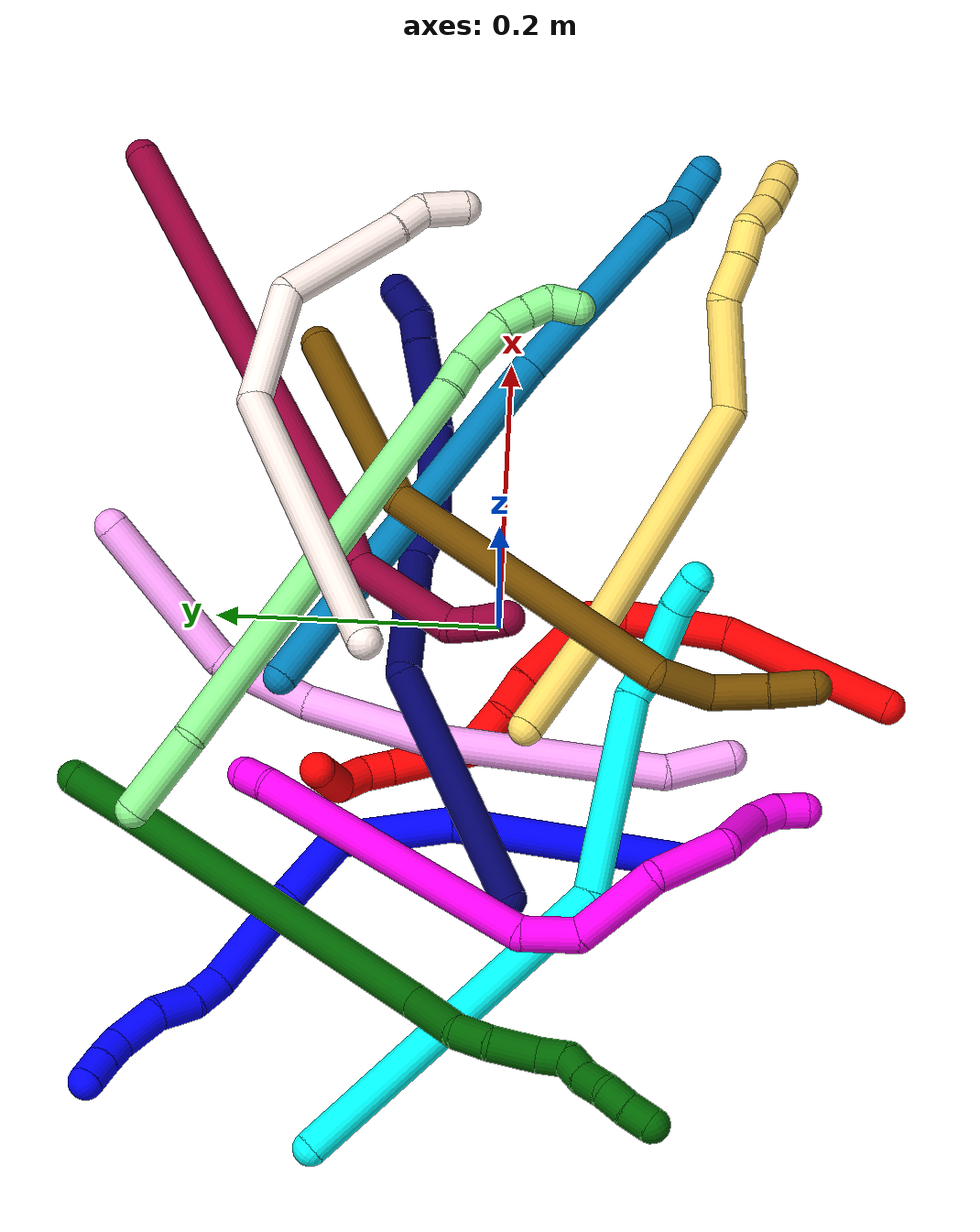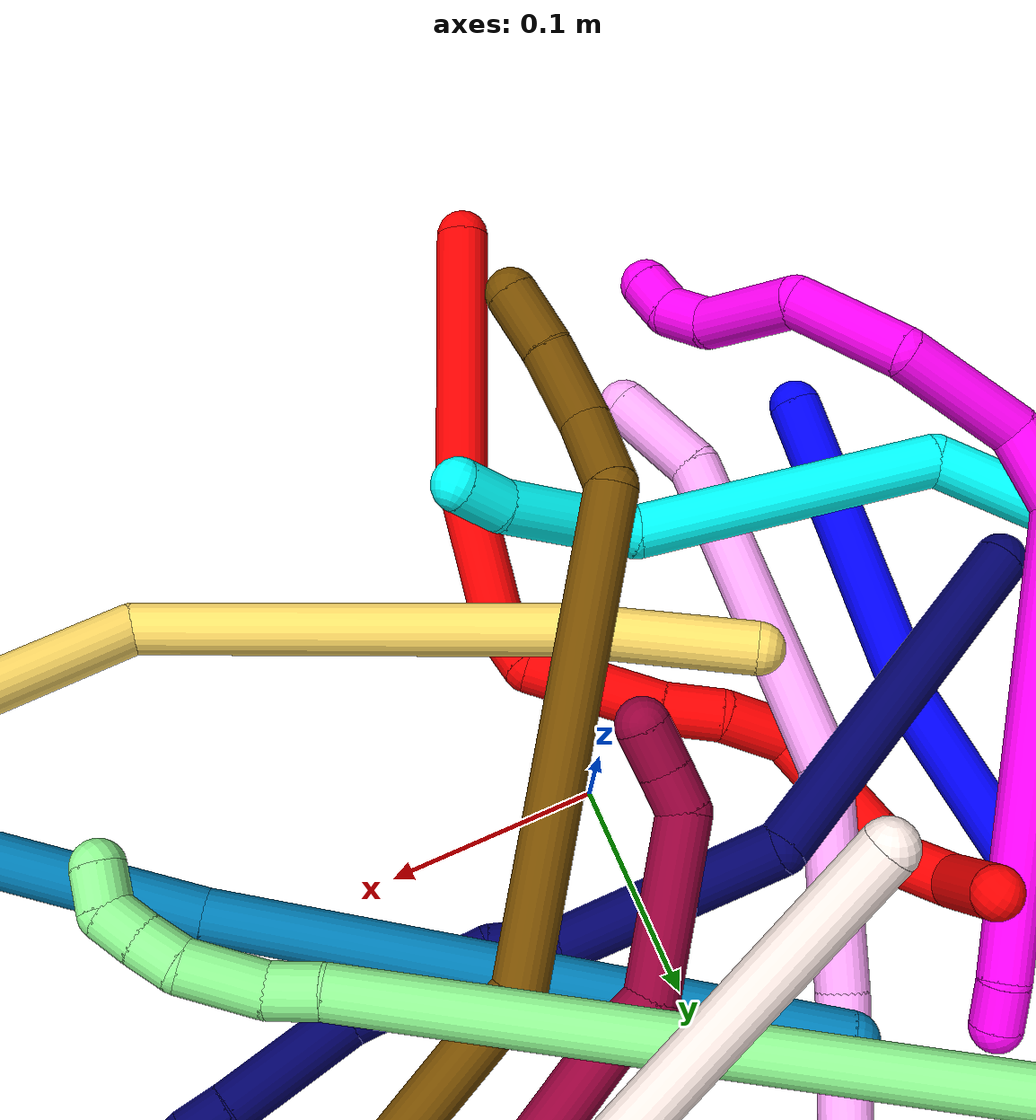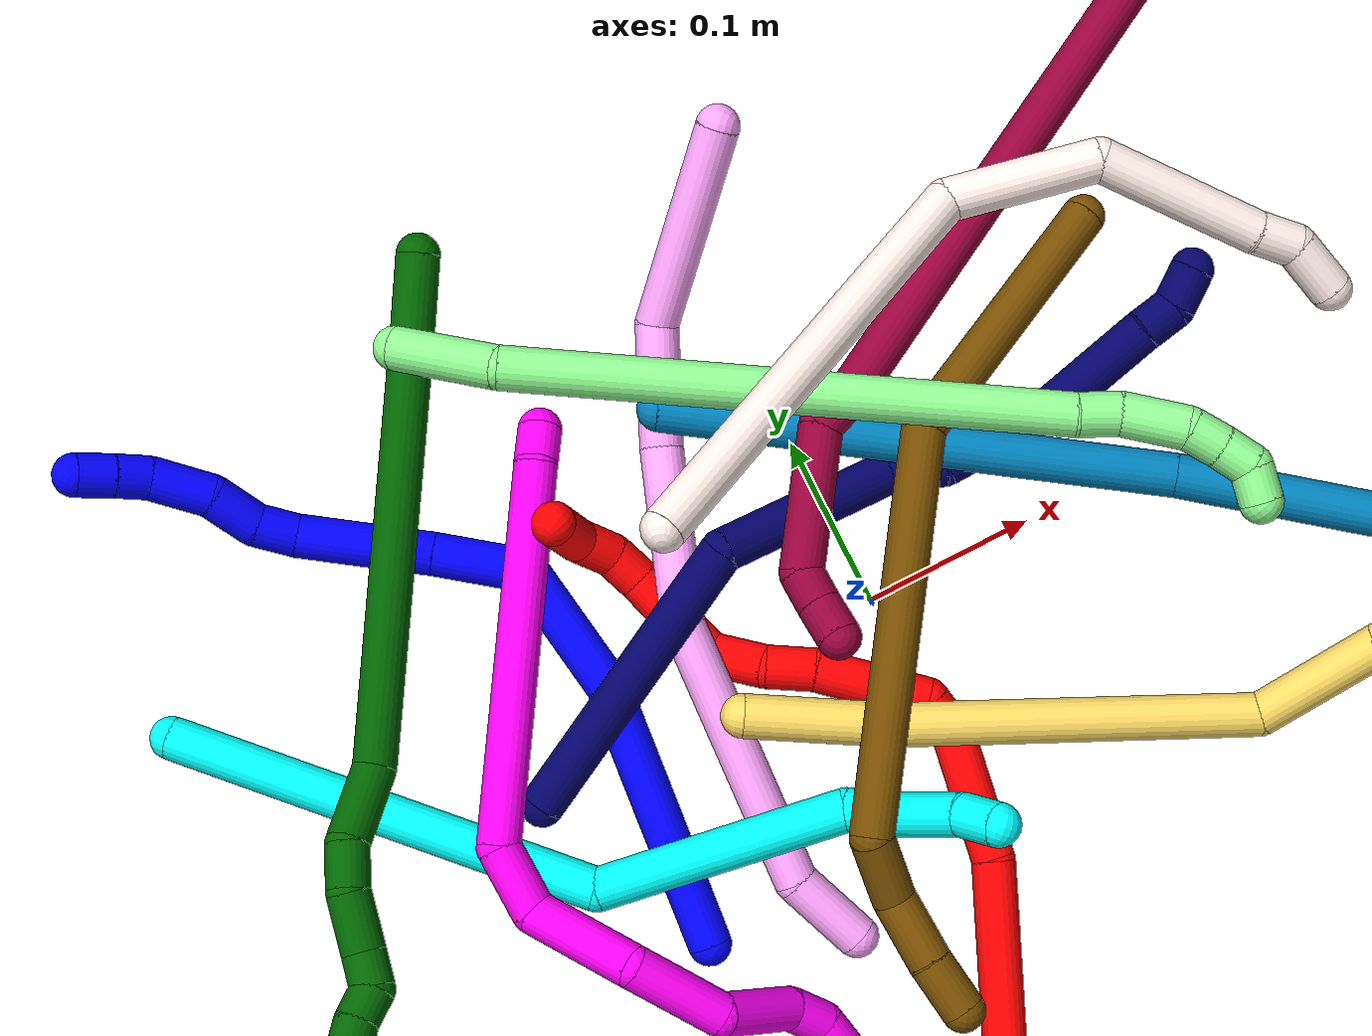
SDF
<sdf version="1.7">
 <world name="default">
  <plugin name="TubeGeneratorPlugin" filename="libtube_generator_plugin.so"/>
  <model name="photoneo_s_sensor">
   <static>1</static>
   <pose>0 0 2 1.57079 1.57079 3.14159</pose>
   <link name="link">
    <inertial><mass>0.1</mass></inertial>
    <sensor name="sensor" type="depth">
     <update_rate>30</update_rate>
     <camera>
      <horizontal_fov>1.22</horizontal_fov>
      <image><width>1920</width><height>1200</height><format>B8G8R8</format></image>
      <clip><near>0.1</near><far>4</far></clip>
      <depth_camera><output>points</output></depth_camera>
     </camera>
     <plugin name="camera_plugin" filename="libgazebo_ros_depth_camera.so">
      <baseline>0.2</baseline>
      <alwaysOn>1</alwaysOn>
      <updateRate>0.0</updateRate>
      <cameraName>camera_ir</cameraName>
      <imageTopicName>/camera/color/image_raw</imageTopicName>
      <cameraInfoTopicName>/camera/color/camera_info</cameraInfoTopicName>
      <depthImageTopicName>/camera/depth/image_raw</depthImageTopicName>
      <depthImageCameraInfoTopicName>/camera/depth/camera_info</depthImageCameraInfoTopicName>
      <pointCloudTopicName>/camera/depth/points</pointCloudTopicName>
      <frameName>fr_optical</frameName>
      <pointCloudCutoff>0.1</pointCloudCutoff>
      <pointCloudCutoffMax>2.0</pointCloudCutoffMax>
      <distortionK1>0</distortionK1>
      <distortionK2>0</distortionK2>
      <distortionK3>0</distortionK3>
      <distortionT1>0</distortionT1>
      <distortionT2>0</distortionT2>
      <CxPrime>0</CxPrime>
      <Cx>0</Cx>
      <Cy>0</Cy>
      <focalLength>0</focalLength>
      <hackBaseline>0</hackBaseline>
     </plugin>
    </sensor>
   </link>
  </model>
  <gravity>0 0 -9.8</gravity>
  <magnetic_field>6e-06 2.3e-05 -4.2e-05</magnetic_field>
  <atmosphere type="adiabatic"/>
  <physics name="default_physics" default="0" type="ode">
   <max_step_size>0.003</max_step_size>
   <real_time_factor>1</real_time_factor>
   <real_time_update_rate>1000</real_time_update_rate>
   <max_contacts>10000</max_contacts>
   <ode>
    <solver>
     <type>quick</type>
     <iters>100</iters>
     <sor>1.3</sor>
     <use_dynamic_moi_rescaling>0</use_dynamic_moi_rescaling>
    </solver>
    <constraints>
     <contact_max_correcting_vel>0</contact_max_correcting_vel>
     <contact_surface_layer>0.001</contact_surface_layer>
     <cfm>0</cfm>
     <erp>0.2</erp>
    </constraints>
   </ode>
  </physics>
  <scene><ambient>0.4 0.4 0.4 1</ambient><background>0.7 0.7 0.7 1</background><shadows>0</shadows></scene>
  <audio><device>default</device></audio>
  <spherical_coordinates>
   <surface_model>EARTH_WGS84</surface_model>
   <latitude_deg>0</latitude_deg>
   <longitude_deg>0</longitude_deg>
   <elevation>0</elevation>
   <heading_deg>0</heading_deg>
  </spherical_coordinates>
  <model name="bin">
   <static>1</static>
   <link name="bottom">
    <collision name="collision-bottom">
     <pose>0 0 -0.01 0 -0 0</pose>
     <geometry><box><size>0.8 0.6 0.02</size></box></geometry>
     <surface>
      <friction><ode><mu>100</mu><mu2>100</mu2></ode></friction>
      <contact><collide_bitmask>65535</collide_bitmask></contact>
     </surface>
    </collision>
   </link>
   <link name="west_wall">
    <collision name="collision-west_wall">
     <pose>-0.41 0 0.1 0 -0 0</pose>
     <geometry><box><size>0.02 0.6 0.2</size></box></geometry>
     <surface>
      <friction><ode><mu>100</mu><mu2>100</mu2></ode></friction>
      <contact><collide_bitmask>65535</collide_bitmask></contact>
     </surface>
    </collision>
   </link>
   <link name="east_wall">
    <collision name="collision-east_wall">
     <pose>0.41 0 0.1 0 -0 0</pose>
     <geometry><box><size>0.02 0.6 0.2</size></box></geometry>
     <surface>
      <friction><ode><mu>100</mu><mu2>100</mu2></ode></friction>
      <contact><collide_bitmask>65535</collide_bitmask></contact>
     </surface>
    </collision>
   </link>
   <link name="south_wall">
    <collision name="collision-south_wall">
     <pose>0 -0.31 0.1 0 -0 0</pose>
     <geometry><box><size>0.8 0.02 0.2</size></box></geometry>
     <surface>
      <friction><ode><mu>100</mu><mu2>100</mu2></ode></friction>
      <contact><collide_bitmask>65535</collide_bitmask></contact>
     </surface>
    </collision>
   </link>
   <link name="north_wall">
    <collision name="collision-north_wall">
     <pose>0 0.31 0.1 0 -0 0</pose>
     <geometry><box><size>0.8 0.02 0.2</size></box></geometry>
     <surface>
      <friction><ode><mu>100</mu><mu2>100</mu2></ode></friction>
      <contact><collide_bitmask>65535</collide_bitmask></contact>
     </surface>
    </collision>
   </link>
  </model>
  <model name="1">
   <static>0</static>
   <link name="1">
    <collision name="collision-cylinder-e_1_1_4">
     <pose>-0.033387 0.044102 0.056152 -0.665776 -0.437388 0.153386</pose>
     <geometry><cylinder><radius>0.0125</radius><length>0.157642</length></cylinder></geometry>
     <surface>
      <friction><ode><mu>1.16</mu><mu2>1.16</mu2><slip1>0</slip1><slip2>0</slip2></ode></friction>
      <contact><ode><kp>1e+06</kp><kd>1</kd><max_vel>0</max_vel><min_depth>0.001</min_depth></ode></contact>
     </surface>
    </collision>
    <visual name="visual-cylinder-e_1_1_4">
     <pose>-0.033387 0.044102 0.056152 -0.665776 -0.437388 0.153386</pose>
     <geometry><cylinder><radius>0.0125</radius><length>0.157642</length></cylinder></geometry>
     <material><ambient>0 0 1 1</ambient></material>
    </visual>
    <collision name="collision-cylinder-e_2_4_5">
     <pose>-0.074931 0.105935 0.147477 -0.466927 -0.204237 0.048727</pose>
     <geometry><cylinder><radius>0.0125</radius><length>0.080449</length></cylinder></geometry>
     <surface>
      <friction><ode><mu>1.16</mu><mu2>1.16</mu2><slip1>0</slip1><slip2>0</slip2></ode></friction>
      <contact><ode><kp>1e+06</kp><kd>1</kd><max_vel>0</max_vel><min_depth>0.001</min_depth></ode></contact>
     </surface>
    </collision>
    <visual name="visual-cylinder-e_2_4_5">
     <pose>-0.074931 0.105935 0.147477 -0.466927 -0.204237 0.048727</pose>
     <geometry><cylinder><radius>0.0125</radius><length>0.080449</length></cylinder></geometry>
     <material><ambient>0 0 1 1</ambient></material>
    </visual>
    <collision name="collision-cylinder-e_3_5_6">
     <pose>-0.068763 0.134014 0.202483 -0.480911 0.569574 -0.143316</pose>
     <geometry><cylinder><radius>0.0125</radius><length>0.053132</length></cylinder></geometry>
     <surface>
      <friction><ode><mu>1.16</mu><mu2>1.16</mu2><slip1>0</slip1><slip2>0</slip2></ode></friction>
      <contact><ode><kp>1e+06</kp><kd>1</kd><max_vel>0</max_vel><min_depth>0.001</min_depth></ode></contact>
     </surface>
    </collision>
    <visual name="visual-cylinder-e_3_5_6">
     <pose>-0.068763 0.134014 0.202483 -0.480911 0.569574 -0.143316</pose>
     <geometry><cylinder><radius>0.0125</radius><length>0.053132</length></cylinder></geometry>
     <material><ambient>0 0 1 1</ambient></material>
    </visual>
    <collision name="collision-cylinder-e_4_6_7">
     <pose>-0.031924 0.159634 0.250251 -0.500299 0.615527 -0.162073</pose>
     <geometry><cylinder><radius>0.0125</radius><length>0.077981</length></cylinder></geometry>
     <surface>
      <friction><ode><mu>1.16</mu><mu2>1.16</mu2><slip1>0</slip1><slip2>0</slip2></ode></friction>
      <contact><ode><kp>1e+06</kp><kd>1</kd><max_vel>0</max_vel><min_depth>0.001</min_depth></ode></contact>
     </surface>
    </collision>
    <visual name="visual-cylinder-e_4_6_7">
     <pose>-0.031924 0.159634 0.250251 -0.500299 0.615527 -0.162073</pose>
     <geometry><cylinder><radius>0.0125</radius><length>0.077981</length></cylinder></geometry>
     <material><ambient>0 0 1 1</ambient></material>
    </visual>
    <collision name="collision-cylinder-e_5_7_8">
     <pose>-0.003623 0.182466 0.285745 -0.785404 0.496177 -0.209083</pose>
     <geometry><cylinder><radius>0.0125</radius><length>0.02432</length></cylinder></geometry>
     <surface>
      <friction><ode><mu>1.16</mu><mu2>1.16</mu2><slip1>0</slip1><slip2>0</slip2></ode></friction>
      <contact><ode><kp>1e+06</kp><kd>1</kd><max_vel>0</max_vel><min_depth>0.001</min_depth></ode></contact>
     </surface>
    </collision>
    <visual name="visual-cylinder-e_5_7_8">
     <pose>-0.003623 0.182466 0.285745 -0.785404 0.496177 -0.209083</pose>
     <geometry><cylinder><radius>0.0125</radius><length>0.02432</length></cylinder></geometry>
     <material><ambient>0 0 1 1</ambient></material>
    </visual>
    <collision name="collision-cylinder-e_6_8_9">
     <pose>0.004477 0.201177 0.30258 -0.877043 0.158017 -0.074226</pose>
     <geometry><cylinder><radius>0.0125</radius><length>0.02937</length></cylinder></geometry>
     <surface>
      <friction><ode><mu>1.16</mu><mu2>1.16</mu2><slip1>0</slip1><slip2>0</slip2></ode></friction>
      <contact><ode><kp>1e+06</kp><kd>1</kd><max_vel>0</max_vel><min_depth>0.001</min_depth></ode></contact>
     </surface>
    </collision>
    <visual name="visual-cylinder-e_6_8_9">
     <pose>0.004477 0.201177 0.30258 -0.877043 0.158017 -0.074226</pose>
     <geometry><cylinder><radius>0.0125</radius><length>0.02937</length></cylinder></geometry>
     <material><ambient>0 0 1 1</ambient></material>
    </visual>
    <collision name="collision-cylinder-e_7_9_10">
     <pose>0.014847 0.223496 0.323175 -0.778593 0.469014 -0.195387</pose>
     <geometry><cylinder><radius>0.0125</radius><length>0.035658</length></cylinder></geometry>
     <surface>
      <friction><ode><mu>1.16</mu><mu2>1.16</mu2><slip1>0</slip1><slip2>0</slip2></ode></friction>
      <contact><ode><kp>1e+06</kp><kd>1</kd><max_vel>0</max_vel><min_depth>0.001</min_depth></ode></contact>
     </surface>
    </collision>
    <visual name="visual-cylinder-e_7_9_10">
     <pose>0.014847 0.223496 0.323175 -0.778593 0.469014 -0.195387</pose>
     <geometry><cylinder><radius>0.0125</radius><length>0.035658</length></cylinder></geometry>
     <material><ambient>0 0 1 1</ambient></material>
    </visual>
    <collision name="collision-cylinder-e_8_10_11">
     <pose>0.029128 0.241407 0.338487 -1.03641 0.671203 -0.392629</pose>
     <geometry><cylinder><radius>0.0125</radius><length>0.02001</length></cylinder></geometry>
     <surface>
      <friction><ode><mu>1.16</mu><mu2>1.16</mu2><slip1>0</slip1><slip2>0</slip2></ode></friction>
      <contact><ode><kp>1e+06</kp><kd>1</kd><max_vel>0</max_vel><min_depth>0.001</min_depth></ode></contact>
     </surface>
    </collision>
    <visual name="visual-cylinder-e_8_10_11">
     <pose>0.029128 0.241407 0.338487 -1.03641 0.671203 -0.392629</pose>
     <geometry><cylinder><radius>0.0125</radius><length>0.02001</length></cylinder></geometry>
     <material><ambient>0 0 1 1</ambient></material>
    </visual>
    <collision name="collision-cylinder-e_9_11_2">
     <pose>0.04237 0.255011 0.346784 -1.01024 0.714051 -0.406823</pose>
     <geometry><cylinder><radius>0.0125</radius><length>0.021438</length></cylinder></geometry>
     <surface>
      <friction><ode><mu>1.16</mu><mu2>1.16</mu2><slip1>0</slip1><slip2>0</slip2></ode></friction>
      <contact><ode><kp>1e+06</kp><kd>1</kd><max_vel>0</max_vel><min_depth>0.001</min_depth></ode></contact>
     </surface>
    </collision>
    <visual name="visual-cylinder-e_9_11_2">
     <pose>0.04237 0.255011 0.346784 -1.01024 0.714051 -0.406823</pose>
     <geometry><cylinder><radius>0.0125</radius><length>0.021438</length></cylinder></geometry>
     <material><ambient>0 0 1 1</ambient></material>
    </visual>
    <collision name="collision-sphere-2">
     <pose>0.04939 0.261872 0.35109 0 -0 0</pose>
     <geometry><sphere><radius>0.0125</radius></sphere></geometry>
     <surface>
      <friction><ode><mu>1.16</mu><mu2>1.16</mu2><slip1>0</slip1><slip2>0</slip2></ode></friction>
      <contact><ode><kp>1e+06</kp><kd>1</kd><max_vel>0</max_vel><min_depth>0.001</min_depth></ode></contact>
     </surface>
    </collision>
    <visual name="visual-sphere-2">
     <pose>0.04939 0.261872 0.35109 0 -0 0</pose>
     <geometry><sphere><radius>0.0125</radius></sphere></geometry>
     <material><ambient>0 0 1 1</ambient></material>
    </visual>
    <collision name="collision-sphere-11">
     <pose>0.03535 0.24815 0.342477 0 -0 0</pose>
     <geometry><sphere><radius>0.0125</radius></sphere></geometry>
     <surface>
      <friction><ode><mu>1.16</mu><mu2>1.16</mu2><slip1>0</slip1><slip2>0</slip2></ode></friction>
      <contact><ode><kp>1e+06</kp><kd>1</kd><max_vel>0</max_vel><min_depth>0.001</min_depth></ode></contact>
     </surface>
    </collision>
    <visual name="visual-sphere-11">
     <pose>0.03535 0.24815 0.342477 0 -0 0</pose>
     <geometry><sphere><radius>0.0125</radius></sphere></geometry>
     <material><ambient>0 0 1 1</ambient></material>
    </visual>
    <collision name="collision-sphere-10">
     <pose>0.022905 0.234665 0.334496 0 -0 0</pose>
     <geometry><sphere><radius>0.0125</radius></sphere></geometry>
     <surface>
      <friction><ode><mu>1.16</mu><mu2>1.16</mu2><slip1>0</slip1><slip2>0</slip2></ode></friction>
      <contact><ode><kp>1e+06</kp><kd>1</kd><max_vel>0</max_vel><min_depth>0.001</min_depth></ode></contact>
     </surface>
    </collision>
    <visual name="visual-sphere-10">
     <pose>0.022905 0.234665 0.334496 0 -0 0</pose>
     <geometry><sphere><radius>0.0125</radius></sphere></geometry>
     <material><ambient>0 0 1 1</ambient></material>
    </visual>
    <collision name="collision-sphere-9">
     <pose>0.006788 0.212328 0.311853 0 -0 0</pose>
     <geometry><sphere><radius>0.0125</radius></sphere></geometry>
     <surface>
      <friction><ode><mu>1.16</mu><mu2>1.16</mu2><slip1>0</slip1><slip2>0</slip2></ode></friction>
      <contact><ode><kp>1e+06</kp><kd>1</kd><max_vel>0</max_vel><min_depth>0.001</min_depth></ode></contact>
     </surface>
    </collision>
    <visual name="visual-sphere-9">
     <pose>0.006788 0.212328 0.311853 0 -0 0</pose>
     <geometry><sphere><radius>0.0125</radius></sphere></geometry>
     <material><ambient>0 0 1 1</ambient></material>
    </visual>
    <collision name="collision-sphere-4">
     <pose>-0.066773 0.088204 0.112305 0 -0 0</pose>
     <geometry><sphere><radius>0.0125</radius></sphere></geometry>
     <surface>
      <friction><ode><mu>1.16</mu><mu2>1.16</mu2><slip1>0</slip1><slip2>0</slip2></ode></friction>
      <contact><ode><kp>1e+06</kp><kd>1</kd><max_vel>0</max_vel><min_depth>0.001</min_depth></ode></contact>
     </surface>
    </collision>
    <visual name="visual-sphere-4">
     <pose>-0.066773 0.088204 0.112305 0 -0 0</pose>
     <geometry><sphere><radius>0.0125</radius></sphere></geometry>
     <material><ambient>0 0 1 1</ambient></material>
    </visual>
    <collision name="collision-sphere-1">
     <geometry><sphere><radius>0.0125</radius></sphere></geometry>
     <surface>
      <friction><ode><mu>1.16</mu><mu2>1.16</mu2><slip1>0</slip1><slip2>0</slip2></ode></friction>
      <contact><ode><kp>1e+06</kp><kd>1</kd><max_vel>0</max_vel><min_depth>0.001</min_depth></ode></contact>
     </surface>
    </collision>
    <visual name="visual-sphere-1">
     <geometry><sphere><radius>0.0125</radius></sphere></geometry>
     <material><ambient>0 0 1 1</ambient></material>
    </visual>
    <collision name="collision-sphere-8">
     <pose>0.002166 0.190027 0.293306 0 -0 0</pose>
     <geometry><sphere><radius>0.0125</radius></sphere></geometry>
     <surface>
      <friction><ode><mu>1.16</mu><mu2>1.16</mu2><slip1>0</slip1><slip2>0</slip2></ode></friction>
      <contact><ode><kp>1e+06</kp><kd>1</kd><max_vel>0</max_vel><min_depth>0.001</min_depth></ode></contact>
     </surface>
    </collision>
    <visual name="visual-sphere-8">
     <pose>0.002166 0.190027 0.293306 0 -0 0</pose>
     <geometry><sphere><radius>0.0125</radius></sphere></geometry>
     <material><ambient>0 0 1 1</ambient></material>
    </visual>
    <collision name="collision-sphere-5">
     <pose>-0.08309 0.123665 0.182649 0 -0 0</pose>
     <geometry><sphere><radius>0.0125</radius></sphere></geometry>
     <surface>
      <friction><ode><mu>1.16</mu><mu2>1.16</mu2><slip1>0</slip1><slip2>0</slip2></ode></friction>
      <contact><ode><kp>1e+06</kp><kd>1</kd><max_vel>0</max_vel><min_depth>0.001</min_depth></ode></contact>
     </surface>
    </collision>
    <visual name="visual-sphere-5">
     <pose>-0.08309 0.123665 0.182649 0 -0 0</pose>
     <geometry><sphere><radius>0.0125</radius></sphere></geometry>
     <material><ambient>0 0 1 1</ambient></material>
    </visual>
    <collision name="collision-sphere-6">
     <pose>-0.054437 0.144363 0.222318 0 -0 0</pose>
     <geometry><sphere><radius>0.0125</radius></sphere></geometry>
     <surface>
      <friction><ode><mu>1.16</mu><mu2>1.16</mu2><slip1>0</slip1><slip2>0</slip2></ode></friction>
      <contact><ode><kp>1e+06</kp><kd>1</kd><max_vel>0</max_vel><min_depth>0.001</min_depth></ode></contact>
     </surface>
    </collision>
    <visual name="visual-sphere-6">
     <pose>-0.054437 0.144363 0.222318 0 -0 0</pose>
     <geometry><sphere><radius>0.0125</radius></sphere></geometry>
     <material><ambient>0 0 1 1</ambient></material>
    </visual>
    <collision name="collision-sphere-7">
     <pose>-0.009412 0.174905 0.278184 0 -0 0</pose>
     <geometry><sphere><radius>0.0125</radius></sphere></geometry>
     <surface>
      <friction><ode><mu>1.16</mu><mu2>1.16</mu2><slip1>0</slip1><slip2>0</slip2></ode></friction>
      <contact><ode><kp>1e+06</kp><kd>1</kd><max_vel>0</max_vel><min_depth>0.001</min_depth></ode></contact>
     </surface>
    </collision>
    <visual name="visual-sphere-7">
     <pose>-0.009412 0.174905 0.278184 0 -0 0</pose>
     <geometry><sphere><radius>0.0125</radius></sphere></geometry>
     <material><ambient>0 0 1 1</ambient></material>
    </visual>
    <inertial>
     <pose>-0.030741 0.127313 0.185114 0 -0 0</pose>
     <mass>0.5</mass>
     <inertia>
      <ixx>0.000444</ixx>
      <ixy>0</ixy>
      <ixz>0</ixz>
      <iyy>0.000434</iyy>
      <iyz>0</iyz>
      <izz>-9.9e-05</izz>
     </inertia>
    </inertial>
   </link>
   <pose>-0.169551 -0.131616 0.011797 2.12205 -0.118477 -2.79397</pose>
  </model>
  <model name="2">
   <static>0</static>
   <link name="2">
    <collision name="collision-cylinder-e_1_1_4">
     <pose>-0.040839 0.022211 0.04113 -0.495154 -0.718082 0.189162</pose>
     <geometry><cylinder><radius>0.0125</radius><length>0.124142</length></cylinder></geometry>
     <surface>
      <friction><ode><mu>1.16</mu><mu2>1.16</mu2><slip1>0</slip1><slip2>0</slip2></ode></friction>
      <contact><ode><kp>1e+06</kp><kd>1</kd><max_vel>0</max_vel><min_depth>0.001</min_depth></ode></contact>
     </surface>
    </collision>
    <visual name="visual-cylinder-e_1_1_4">
     <pose>-0.040839 0.022211 0.04113 -0.495154 -0.718082 0.189162</pose>
     <geometry><cylinder><radius>0.0125</radius><length>0.124142</length></cylinder></geometry>
     <material><ambient>1 0 0 1</ambient></material>
    </visual>
    <collision name="collision-cylinder-e_2_4_5">
     <pose>-0.102853 0.06613 0.103023 -0.807619 -0.613988 0.269277</pose>
     <geometry><cylinder><radius>0.0125</radius><length>0.073505</length></cylinder></geometry>
     <surface>
      <friction><ode><mu>1.16</mu><mu2>1.16</mu2><slip1>0</slip1><slip2>0</slip2></ode></friction>
      <contact><ode><kp>1e+06</kp><kd>1</kd><max_vel>0</max_vel><min_depth>0.001</min_depth></ode></contact>
     </surface>
    </collision>
    <visual name="visual-cylinder-e_2_4_5">
     <pose>-0.102853 0.06613 0.103023 -0.807619 -0.613988 0.269277</pose>
     <geometry><cylinder><radius>0.0125</radius><length>0.073505</length></cylinder></geometry>
     <material><ambient>1 0 0 1</ambient></material>
    </visual>
    <collision name="collision-cylinder-e_3_5_6">
     <pose>-0.133886 0.096148 0.125522 -1.36507 -0.859992 0.713668</pose>
     <geometry><cylinder><radius>0.0125</radius><length>0.02602</length></cylinder></geometry>
     <surface>
      <friction><ode><mu>1.16</mu><mu2>1.16</mu2><slip1>0</slip1><slip2>0</slip2></ode></friction>
      <contact><ode><kp>1e+06</kp><kd>1</kd><max_vel>0</max_vel><min_depth>0.001</min_depth></ode></contact>
     </surface>
    </collision>
    <visual name="visual-cylinder-e_3_5_6">
     <pose>-0.133886 0.096148 0.125522 -1.36507 -0.859992 0.713668</pose>
     <geometry><cylinder><radius>0.0125</radius><length>0.02602</length></cylinder></geometry>
     <material><ambient>1 0 0 1</ambient></material>
    </visual>
    <collision name="collision-cylinder-e_4_6_7">
     <pose>-0.153543 0.133927 0.117036 -1.90461 -0.30433 0.424489</pose>
     <geometry><cylinder><radius>0.0125</radius><length>0.065388</length></cylinder></geometry>
     <surface>
      <friction><ode><mu>1.16</mu><mu2>1.16</mu2><slip1>0</slip1><slip2>0</slip2></ode></friction>
      <contact><ode><kp>1e+06</kp><kd>1</kd><max_vel>0</max_vel><min_depth>0.001</min_depth></ode></contact>
     </surface>
    </collision>
    <visual name="visual-cylinder-e_4_6_7">
     <pose>-0.153543 0.133927 0.117036 -1.90461 -0.30433 0.424489</pose>
     <geometry><cylinder><radius>0.0125</radius><length>0.065388</length></cylinder></geometry>
     <material><ambient>1 0 0 1</ambient></material>
    </visual>
    <collision name="collision-cylinder-e_5_7_8">
     <pose>-0.165566 0.175805 0.100568 -2.03731 -0.158918 0.257079</pose>
     <geometry><cylinder><radius>0.0125</radius><length>0.02814</length></cylinder></geometry>
     <surface>
      <friction><ode><mu>1.16</mu><mu2>1.16</mu2><slip1>0</slip1><slip2>0</slip2></ode></friction>
      <contact><ode><kp>1e+06</kp><kd>1</kd><max_vel>0</max_vel><min_depth>0.001</min_depth></ode></contact>
     </surface>
    </collision>
    <visual name="visual-cylinder-e_5_7_8">
     <pose>-0.165566 0.175805 0.100568 -2.03731 -0.158918 0.257079</pose>
     <geometry><cylinder><radius>0.0125</radius><length>0.02814</length></cylinder></geometry>
     <material><ambient>1 0 0 1</ambient></material>
    </visual>
    <collision name="collision-cylinder-e_6_8_9">
     <pose>-0.16818 0.204904 0.091628 -1.73067 -0.022914 0.026905</pose>
     <geometry><cylinder><radius>0.0125</radius><length>0.033823</length></cylinder></geometry>
     <surface>
      <friction><ode><mu>1.16</mu><mu2>1.16</mu2><slip1>0</slip1><slip2>0</slip2></ode></friction>
      <contact><ode><kp>1e+06</kp><kd>1</kd><max_vel>0</max_vel><min_depth>0.001</min_depth></ode></contact>
     </surface>
    </collision>
    <visual name="visual-cylinder-e_6_8_9">
     <pose>-0.16818 0.204904 0.091628 -1.73067 -0.022914 0.026905</pose>
     <geometry><cylinder><radius>0.0125</radius><length>0.033823</length></cylinder></geometry>
     <material><ambient>1 0 0 1</ambient></material>
    </visual>
    <collision name="collision-cylinder-e_7_9_10">
     <pose>-0.184824 0.245454 0.093493 -1.38206 -0.589815 0.492283</pose>
     <geometry><cylinder><radius>0.0125</radius><length>0.058454</length></cylinder></geometry>
     <surface>
      <friction><ode><mu>1.16</mu><mu2>1.16</mu2><slip1>0</slip1><slip2>0</slip2></ode></friction>
      <contact><ode><kp>1e+06</kp><kd>1</kd><max_vel>0</max_vel><min_depth>0.001</min_depth></ode></contact>
     </surface>
    </collision>
    <visual name="visual-cylinder-e_7_9_10">
     <pose>-0.184824 0.245454 0.093493 -1.38206 -0.589815 0.492283</pose>
     <geometry><cylinder><radius>0.0125</radius><length>0.058454</length></cylinder></geometry>
     <material><ambient>1 0 0 1</ambient></material>
    </visual>
    <collision name="collision-cylinder-e_8_10_11">
     <pose>-0.208308 0.276805 0.09784 -1.59888 -0.767135 0.786826</pose>
     <geometry><cylinder><radius>0.0125</radius><length>0.020826</length></cylinder></geometry>
     <surface>
      <friction><ode><mu>1.16</mu><mu2>1.16</mu2><slip1>0</slip1><slip2>0</slip2></ode></friction>
      <contact><ode><kp>1e+06</kp><kd>1</kd><max_vel>0</max_vel><min_depth>0.001</min_depth></ode></contact>
     </surface>
    </collision>
    <visual name="visual-cylinder-e_8_10_11">
     <pose>-0.208308 0.276805 0.09784 -1.59888 -0.767135 0.786826</pose>
     <geometry><cylinder><radius>0.0125</radius><length>0.020826</length></cylinder></geometry>
     <material><ambient>1 0 0 1</ambient></material>
    </visual>
    <collision name="collision-cylinder-e_9_11_12">
     <pose>-0.223741 0.291389 0.092796 -2.16906 -0.763049 1.2984</pose>
     <geometry><cylinder><radius>0.0125</radius><length>0.023745</length></cylinder></geometry>
     <surface>
      <friction><ode><mu>1.16</mu><mu2>1.16</mu2><slip1>0</slip1><slip2>0</slip2></ode></friction>
      <contact><ode><kp>1e+06</kp><kd>1</kd><max_vel>0</max_vel><min_depth>0.001</min_depth></ode></contact>
     </surface>
    </collision>
    <visual name="visual-cylinder-e_9_11_12">
     <pose>-0.223741 0.291389 0.092796 -2.16906 -0.763049 1.2984</pose>
     <geometry><cylinder><radius>0.0125</radius><length>0.023745</length></cylinder></geometry>
     <material><ambient>1 0 0 1</ambient></material>
    </visual>
    <collision name="collision-cylinder-e_10_12_2">
     <pose>-0.251798 0.295249 0.076852 2.85868 -1.04304 -2.6557</pose>
     <geometry><cylinder><radius>0.0125</radius><length>0.045956</length></cylinder></geometry>
     <surface>
      <friction><ode><mu>1.16</mu><mu2>1.16</mu2><slip1>0</slip1><slip2>0</slip2></ode></friction>
      <contact><ode><kp>1e+06</kp><kd>1</kd><max_vel>0</max_vel><min_depth>0.001</min_depth></ode></contact>
     </surface>
    </collision>
    <visual name="visual-cylinder-e_10_12_2">
     <pose>-0.251798 0.295249 0.076852 2.85868 -1.04304 -2.6557</pose>
     <geometry><cylinder><radius>0.0125</radius><length>0.045956</length></cylinder></geometry>
     <material><ambient>1 0 0 1</ambient></material>
    </visual>
    <collision name="collision-sphere-2">
     <pose>-0.27165 0.292019 0.065741 0 -0 0</pose>
     <geometry><sphere><radius>0.0125</radius></sphere></geometry>
     <surface>
      <friction><ode><mu>1.16</mu><mu2>1.16</mu2><slip1>0</slip1><slip2>0</slip2></ode></friction>
      <contact><ode><kp>1e+06</kp><kd>1</kd><max_vel>0</max_vel><min_depth>0.001</min_depth></ode></contact>
     </surface>
    </collision>
    <visual name="visual-sphere-2">
     <pose>-0.27165 0.292019 0.065741 0 -0 0</pose>
     <geometry><sphere><radius>0.0125</radius></sphere></geometry>
     <material><ambient>1 0 0 1</ambient></material>
    </visual>
    <collision name="collision-sphere-12">
     <pose>-0.231947 0.298479 0.087964 0 -0 0</pose>
     <geometry><sphere><radius>0.0125</radius></sphere></geometry>
     <surface>
      <friction><ode><mu>1.16</mu><mu2>1.16</mu2><slip1>0</slip1><slip2>0</slip2></ode></friction>
      <contact><ode><kp>1e+06</kp><kd>1</kd><max_vel>0</max_vel><min_depth>0.001</min_depth></ode></contact>
     </surface>
    </collision>
    <visual name="visual-sphere-12">
     <pose>-0.231947 0.298479 0.087964 0 -0 0</pose>
     <geometry><sphere><radius>0.0125</radius></sphere></geometry>
     <material><ambient>1 0 0 1</ambient></material>
    </visual>
    <collision name="collision-sphere-11">
     <pose>-0.215535 0.284298 0.097629 0 -0 0</pose>
     <geometry><sphere><radius>0.0125</radius></sphere></geometry>
     <surface>
      <friction><ode><mu>1.16</mu><mu2>1.16</mu2><slip1>0</slip1><slip2>0</slip2></ode></friction>
      <contact><ode><kp>1e+06</kp><kd>1</kd><max_vel>0</max_vel><min_depth>0.001</min_depth></ode></contact>
     </surface>
    </collision>
    <visual name="visual-sphere-11">
     <pose>-0.215535 0.284298 0.097629 0 -0 0</pose>
     <geometry><sphere><radius>0.0125</radius></sphere></geometry>
     <material><ambient>1 0 0 1</ambient></material>
    </visual>
    <collision name="collision-sphere-10">
     <pose>-0.20108 0.269311 0.09805 0 -0 0</pose>
     <geometry><sphere><radius>0.0125</radius></sphere></geometry>
     <surface>
      <friction><ode><mu>1.16</mu><mu2>1.16</mu2><slip1>0</slip1><slip2>0</slip2></ode></friction>
      <contact><ode><kp>1e+06</kp><kd>1</kd><max_vel>0</max_vel><min_depth>0.001</min_depth></ode></contact>
     </surface>
    </collision>
    <visual name="visual-sphere-10">
     <pose>-0.20108 0.269311 0.09805 0 -0 0</pose>
     <geometry><sphere><radius>0.0125</radius></sphere></geometry>
     <material><ambient>1 0 0 1</ambient></material>
    </visual>
    <collision name="collision-sphere-9">
     <pose>-0.168568 0.221596 0.088936 0 -0 0</pose>
     <geometry><sphere><radius>0.0125</radius></sphere></geometry>
     <surface>
      <friction><ode><mu>1.16</mu><mu2>1.16</mu2><slip1>0</slip1><slip2>0</slip2></ode></friction>
      <contact><ode><kp>1e+06</kp><kd>1</kd><max_vel>0</max_vel><min_depth>0.001</min_depth></ode></contact>
     </surface>
    </collision>
    <visual name="visual-sphere-9">
     <pose>-0.168568 0.221596 0.088936 0 -0 0</pose>
     <geometry><sphere><radius>0.0125</radius></sphere></geometry>
     <material><ambient>1 0 0 1</ambient></material>
    </visual>
    <collision name="collision-sphere-4">
     <pose>-0.081678 0.044422 0.082259 0 -0 0</pose>
     <geometry><sphere><radius>0.0125</radius></sphere></geometry>
     <surface>
      <friction><ode><mu>1.16</mu><mu2>1.16</mu2><slip1>0</slip1><slip2>0</slip2></ode></friction>
      <contact><ode><kp>1e+06</kp><kd>1</kd><max_vel>0</max_vel><min_depth>0.001</min_depth></ode></contact>
     </surface>
    </collision>
    <visual name="visual-sphere-4">
     <pose>-0.081678 0.044422 0.082259 0 -0 0</pose>
     <geometry><sphere><radius>0.0125</radius></sphere></geometry>
     <material><ambient>1 0 0 1</ambient></material>
    </visual>
    <collision name="collision-sphere-1">
     <geometry><sphere><radius>0.0125</radius></sphere></geometry>
     <surface>
      <friction><ode><mu>1.16</mu><mu2>1.16</mu2><slip1>0</slip1><slip2>0</slip2></ode></friction>
      <contact><ode><kp>1e+06</kp><kd>1</kd><max_vel>0</max_vel><min_depth>0.001</min_depth></ode></contact>
     </surface>
    </collision>
    <visual name="visual-sphere-1">
     <geometry><sphere><radius>0.0125</radius></sphere></geometry>
     <material><ambient>1 0 0 1</ambient></material>
    </visual>
    <collision name="collision-sphere-8">
     <pose>-0.167793 0.188213 0.094319 0 -0 0</pose>
     <geometry><sphere><radius>0.0125</radius></sphere></geometry>
     <surface>
      <friction><ode><mu>1.16</mu><mu2>1.16</mu2><slip1>0</slip1><slip2>0</slip2></ode></friction>
      <contact><ode><kp>1e+06</kp><kd>1</kd><max_vel>0</max_vel><min_depth>0.001</min_depth></ode></contact>
     </surface>
    </collision>
    <visual name="visual-sphere-8">
     <pose>-0.167793 0.188213 0.094319 0 -0 0</pose>
     <geometry><sphere><radius>0.0125</radius></sphere></geometry>
     <material><ambient>1 0 0 1</ambient></material>
    </visual>
    <collision name="collision-sphere-5">
     <pose>-0.124027 0.087839 0.123788 0 -0 0</pose>
     <geometry><sphere><radius>0.0125</radius></sphere></geometry>
     <surface>
      <friction><ode><mu>1.16</mu><mu2>1.16</mu2><slip1>0</slip1><slip2>0</slip2></ode></friction>
      <contact><ode><kp>1e+06</kp><kd>1</kd><max_vel>0</max_vel><min_depth>0.001</min_depth></ode></contact>
     </surface>
    </collision>
    <visual name="visual-sphere-5">
     <pose>-0.124027 0.087839 0.123788 0 -0 0</pose>
     <geometry><sphere><radius>0.0125</radius></sphere></geometry>
     <material><ambient>1 0 0 1</ambient></material>
    </visual>
    <collision name="collision-sphere-6">
     <pose>-0.143746 0.104457 0.127256 0 -0 0</pose>
     <geometry><sphere><radius>0.0125</radius></sphere></geometry>
     <surface>
      <friction><ode><mu>1.16</mu><mu2>1.16</mu2><slip1>0</slip1><slip2>0</slip2></ode></friction>
      <contact><ode><kp>1e+06</kp><kd>1</kd><max_vel>0</max_vel><min_depth>0.001</min_depth></ode></contact>
     </surface>
    </collision>
    <visual name="visual-sphere-6">
     <pose>-0.143746 0.104457 0.127256 0 -0 0</pose>
     <geometry><sphere><radius>0.0125</radius></sphere></geometry>
     <material><ambient>1 0 0 1</ambient></material>
    </visual>
    <collision name="collision-sphere-7">
     <pose>-0.16334 0.163397 0.106816 0 -0 0</pose>
     <geometry><sphere><radius>0.0125</radius></sphere></geometry>
     <surface>
      <friction><ode><mu>1.16</mu><mu2>1.16</mu2><slip1>0</slip1><slip2>0</slip2></ode></friction>
      <contact><ode><kp>1e+06</kp><kd>1</kd><max_vel>0</max_vel><min_depth>0.001</min_depth></ode></contact>
     </surface>
    </collision>
    <visual name="visual-sphere-7">
     <pose>-0.16334 0.163397 0.106816 0 -0 0</pose>
     <geometry><sphere><radius>0.0125</radius></sphere></geometry>
     <material><ambient>1 0 0 1</ambient></material>
    </visual>
    <inertial>
     <pose>-0.137055 0.14271 0.085529 0 -0 0</pose>
     <mass>0.5</mass>
     <inertia>
      <ixx>0.000221</ixx>
      <ixy>0</ixy>
      <ixz>0</ixz>
      <iyy>0.000267</iyy>
      <iyz>0</iyz>
      <izz>3.7e-05</izz>
     </inertia>
    </inertial>
   </link>
   <pose>-0.054416 -0.27444 0.024196 -2.51314 0.826495 -1.88234</pose>
  </model>
  <model name="3">
   <static>0</static>
   <link name="3">
    <collision name="collision-cylinder-e_1_1_4">
     <pose>0.107 -0.072298 -5.3e-05 1.57153 0.976581 0.977193</pose>
     <geometry><cylinder><radius>0.0125</radius><length>0.258272</length></cylinder></geometry>
     <surface>
      <friction><ode><mu>1.16</mu><mu2>1.16</mu2><slip1>0</slip1><slip2>0</slip2></ode></friction>
      <contact><ode><kp>1e+06</kp><kd>1</kd><max_vel>0</max_vel><min_depth>0.001</min_depth></ode></contact>
     </surface>
    </collision>
    <visual name="visual-cylinder-e_1_1_4">
     <pose>0.107 -0.072298 -5.3e-05 1.57153 0.976581 0.977193</pose>
     <geometry><cylinder><radius>0.0125</radius><length>0.258272</length></cylinder></geometry>
     <material><ambient>0.003922 1 0.996078 1</ambient></material>
    </visual>
    <collision name="collision-cylinder-e_2_4_5">
     <pose>0.260638 -0.179842 -0.043647 2.46108 0.694262 1.59246</pose>
     <geometry><cylinder><radius>0.0125</radius><length>0.145783</length></cylinder></geometry>
     <surface>
      <friction><ode><mu>1.16</mu><mu2>1.16</mu2><slip1>0</slip1><slip2>0</slip2></ode></friction>
      <contact><ode><kp>1e+06</kp><kd>1</kd><max_vel>0</max_vel><min_depth>0.001</min_depth></ode></contact>
     </surface>
    </collision>
    <visual name="visual-cylinder-e_2_4_5">
     <pose>0.260638 -0.179842 -0.043647 2.46108 0.694262 1.59246</pose>
     <geometry><cylinder><radius>0.0125</radius><length>0.145783</length></cylinder></geometry>
     <material><ambient>0.003922 1 0.996078 1</ambient></material>
    </visual>
    <collision name="collision-cylinder-e_3_5_6">
     <pose>0.317732 -0.220249 -0.089954 2.06296 1.06043 1.55003</pose>
     <geometry><cylinder><radius>0.0125</radius><length>0.023969</length></cylinder></geometry>
     <surface>
      <friction><ode><mu>1.16</mu><mu2>1.16</mu2><slip1>0</slip1><slip2>0</slip2></ode></friction>
      <contact><ode><kp>1e+06</kp><kd>1</kd><max_vel>0</max_vel><min_depth>0.001</min_depth></ode></contact>
     </surface>
    </collision>
    <visual name="visual-cylinder-e_3_5_6">
     <pose>0.317732 -0.220249 -0.089954 2.06296 1.06043 1.55003</pose>
     <geometry><cylinder><radius>0.0125</radius><length>0.023969</length></cylinder></geometry>
     <material><ambient>0.003922 1 0.996078 1</ambient></material>
    </visual>
    <collision name="collision-cylinder-e_4_6_7">
     <pose>0.350694 -0.227255 -0.099983 2.89263 1.24936 2.79792</pose>
     <geometry><cylinder><radius>0.0125</radius><length>0.047438</length></cylinder></geometry>
     <surface>
      <friction><ode><mu>1.16</mu><mu2>1.16</mu2><slip1>0</slip1><slip2>0</slip2></ode></friction>
      <contact><ode><kp>1e+06</kp><kd>1</kd><max_vel>0</max_vel><min_depth>0.001</min_depth></ode></contact>
     </surface>
    </collision>
    <visual name="visual-cylinder-e_4_6_7">
     <pose>0.350694 -0.227255 -0.099983 2.89263 1.24936 2.79792</pose>
     <geometry><cylinder><radius>0.0125</radius><length>0.047438</length></cylinder></geometry>
     <material><ambient>0.003922 1 0.996078 1</ambient></material>
    </visual>
    <collision name="collision-cylinder-e_5_7_2">
     <pose>0.385408 -0.229726 -0.108275 2.59584 1.47249 2.54255</pose>
     <geometry><cylinder><radius>0.0125</radius><length>0.024539</length></cylinder></geometry>
     <surface>
      <friction><ode><mu>1.16</mu><mu2>1.16</mu2><slip1>0</slip1><slip2>0</slip2></ode></friction>
      <contact><ode><kp>1e+06</kp><kd>1</kd><max_vel>0</max_vel><min_depth>0.001</min_depth></ode></contact>
     </surface>
    </collision>
    <visual name="visual-cylinder-e_5_7_2">
     <pose>0.385408 -0.229726 -0.108275 2.59584 1.47249 2.54255</pose>
     <geometry><cylinder><radius>0.0125</radius><length>0.024539</length></cylinder></geometry>
     <material><ambient>0.003922 1 0.996078 1</ambient></material>
    </visual>
    <collision name="collision-sphere-2">
     <pose>0.397618 -0.230351 -0.109304 0 -0 0</pose>
     <geometry><sphere><radius>0.0125</radius></sphere></geometry>
     <surface>
      <friction><ode><mu>1.16</mu><mu2>1.16</mu2><slip1>0</slip1><slip2>0</slip2></ode></friction>
      <contact><ode><kp>1e+06</kp><kd>1</kd><max_vel>0</max_vel><min_depth>0.001</min_depth></ode></contact>
     </surface>
    </collision>
    <visual name="visual-sphere-2">
     <pose>0.397618 -0.230351 -0.109304 0 -0 0</pose>
     <geometry><sphere><radius>0.0125</radius></sphere></geometry>
     <material><ambient>0.003922 1 0.996078 1</ambient></material>
    </visual>
    <collision name="collision-sphere-7">
     <pose>0.373198 -0.229101 -0.107246 0 -0 0</pose>
     <geometry><sphere><radius>0.0125</radius></sphere></geometry>
     <surface>
      <friction><ode><mu>1.16</mu><mu2>1.16</mu2><slip1>0</slip1><slip2>0</slip2></ode></friction>
      <contact><ode><kp>1e+06</kp><kd>1</kd><max_vel>0</max_vel><min_depth>0.001</min_depth></ode></contact>
     </surface>
    </collision>
    <visual name="visual-sphere-7">
     <pose>0.373198 -0.229101 -0.107246 0 -0 0</pose>
     <geometry><sphere><radius>0.0125</radius></sphere></geometry>
     <material><ambient>0.003922 1 0.996078 1</ambient></material>
    </visual>
    <collision name="collision-sphere-6">
     <pose>0.328189 -0.225408 -0.092721 0 -0 0</pose>
     <geometry><sphere><radius>0.0125</radius></sphere></geometry>
     <surface>
      <friction><ode><mu>1.16</mu><mu2>1.16</mu2><slip1>0</slip1><slip2>0</slip2></ode></friction>
      <contact><ode><kp>1e+06</kp><kd>1</kd><max_vel>0</max_vel><min_depth>0.001</min_depth></ode></contact>
     </surface>
    </collision>
    <visual name="visual-sphere-6">
     <pose>0.328189 -0.225408 -0.092721 0 -0 0</pose>
     <geometry><sphere><radius>0.0125</radius></sphere></geometry>
     <material><ambient>0.003922 1 0.996078 1</ambient></material>
    </visual>
    <collision name="collision-sphere-5">
     <pose>0.307275 -0.215089 -0.087188 0 -0 0</pose>
     <geometry><sphere><radius>0.0125</radius></sphere></geometry>
     <surface>
      <friction><ode><mu>1.16</mu><mu2>1.16</mu2><slip1>0</slip1><slip2>0</slip2></ode></friction>
      <contact><ode><kp>1e+06</kp><kd>1</kd><max_vel>0</max_vel><min_depth>0.001</min_depth></ode></contact>
     </surface>
    </collision>
    <visual name="visual-sphere-5">
     <pose>0.307275 -0.215089 -0.087188 0 -0 0</pose>
     <geometry><sphere><radius>0.0125</radius></sphere></geometry>
     <material><ambient>0.003922 1 0.996078 1</ambient></material>
    </visual>
    <collision name="collision-sphere-1">
     <geometry><sphere><radius>0.0125</radius></sphere></geometry>
     <surface>
      <friction><ode><mu>1.16</mu><mu2>1.16</mu2><slip1>0</slip1><slip2>0</slip2></ode></friction>
      <contact><ode><kp>1e+06</kp><kd>1</kd><max_vel>0</max_vel><min_depth>0.001</min_depth></ode></contact>
     </surface>
    </collision>
    <visual name="visual-sphere-1">
     <geometry><sphere><radius>0.0125</radius></sphere></geometry>
     <material><ambient>0.003922 1 0.996078 1</ambient></material>
    </visual>
    <collision name="collision-sphere-4">
     <pose>0.214001 -0.144596 -0.000107 0 -0 0</pose>
     <geometry><sphere><radius>0.0125</radius></sphere></geometry>
     <surface>
      <friction><ode><mu>1.16</mu><mu2>1.16</mu2><slip1>0</slip1><slip2>0</slip2></ode></friction>
      <contact><ode><kp>1e+06</kp><kd>1</kd><max_vel>0</max_vel><min_depth>0.001</min_depth></ode></contact>
     </surface>
    </collision>
    <visual name="visual-sphere-4">
     <pose>0.214001 -0.144596 -0.000107 0 -0 0</pose>
     <geometry><sphere><radius>0.0125</radius></sphere></geometry>
     <material><ambient>0.003922 1 0.996078 1</ambient></material>
    </visual>
    <inertial>
     <pose>0.198682 -0.133174 -0.031866 0 -0 0</pose>
     <mass>0.5</mass>
     <inertia>
      <ixx>0.001352</ixx>
      <ixy>0</ixy>
      <ixz>0</ixz>
      <iyy>0.001975</iyy>
      <iyz>0</iyz>
      <izz>-0.000451</izz>
     </inertia>
    </inertial>
   </link>
   <pose>-0.387659 0.110822 0.012854 1.54427 -0.715912 -0.782271</pose>
  </model>
  <model name="4">
   <static>0</static>
   <link name="4">
    <collision name="collision-cylinder-e_1_1_4">
     <pose>0.01887 -0.056526 -0.007045 1.69479 0.319893 0.361373</pose>
     <geometry><cylinder><radius>0.0125</radius><length>0.120016</length></cylinder></geometry>
     <surface>
      <friction><ode><mu>1.16</mu><mu2>1.16</mu2><slip1>0</slip1><slip2>0</slip2></ode></friction>
      <contact><ode><kp>1e+06</kp><kd>1</kd><max_vel>0</max_vel><min_depth>0.001</min_depth></ode></contact>
     </surface>
    </collision>
    <visual name="visual-cylinder-e_1_1_4">
     <pose>0.01887 -0.056526 -0.007045 1.69479 0.319893 0.361373</pose>
     <geometry><cylinder><radius>0.0125</radius><length>0.120016</length></cylinder></geometry>
     <material><ambient>1 0.65098 0.996078 1</ambient></material>
    </visual>
    <collision name="collision-cylinder-e_2_4_5">
     <pose>0.039796 -0.146869 -0.003384 1.26418 0.057889 0.042399</pose>
     <geometry><cylinder><radius>0.0125</radius><length>0.07106</length></cylinder></geometry>
     <surface>
      <friction><ode><mu>1.16</mu><mu2>1.16</mu2><slip1>0</slip1><slip2>0</slip2></ode></friction>
      <contact><ode><kp>1e+06</kp><kd>1</kd><max_vel>0</max_vel><min_depth>0.001</min_depth></ode></contact>
     </surface>
    </collision>
    <visual name="visual-cylinder-e_2_4_5">
     <pose>0.039796 -0.146869 -0.003384 1.26418 0.057889 0.042399</pose>
     <geometry><cylinder><radius>0.0125</radius><length>0.07106</length></cylinder></geometry>
     <material><ambient>1 0.65098 0.996078 1</ambient></material>
    </visual>
    <collision name="collision-cylinder-e_3_5_6">
     <pose>0.033837 -0.226234 0.029217 1.12273 -0.157285 -0.099032</pose>
     <geometry><cylinder><radius>0.0125</radius><length>0.102341</length></cylinder></geometry>
     <surface>
      <friction><ode><mu>1.16</mu><mu2>1.16</mu2><slip1>0</slip1><slip2>0</slip2></ode></friction>
      <contact><ode><kp>1e+06</kp><kd>1</kd><max_vel>0</max_vel><min_depth>0.001</min_depth></ode></contact>
     </surface>
    </collision>
    <visual name="visual-cylinder-e_3_5_6">
     <pose>0.033837 -0.226234 0.029217 1.12273 -0.157285 -0.099032</pose>
     <geometry><cylinder><radius>0.0125</radius><length>0.102341</length></cylinder></geometry>
     <material><ambient>1 0.65098 0.996078 1</ambient></material>
    </visual>
    <collision name="collision-cylinder-e_4_6_7">
     <pose>0.043603 -0.333094 0.098152 0.916346 0.226161 0.111898</pose>
     <geometry><cylinder><radius>0.0125</radius><length>0.158592</length></cylinder></geometry>
     <surface>
      <friction><ode><mu>1.16</mu><mu2>1.16</mu2><slip1>0</slip1><slip2>0</slip2></ode></friction>
      <contact><ode><kp>1e+06</kp><kd>1</kd><max_vel>0</max_vel><min_depth>0.001</min_depth></ode></contact>
     </surface>
    </collision>
    <visual name="visual-cylinder-e_4_6_7">
     <pose>0.043603 -0.333094 0.098152 0.916346 0.226161 0.111898</pose>
     <geometry><cylinder><radius>0.0125</radius><length>0.158592</length></cylinder></geometry>
     <material><ambient>1 0.65098 0.996078 1</ambient></material>
    </visual>
    <collision name="collision-cylinder-e_5_7_2">
     <pose>0.070079 -0.405257 0.164747 0.506662 0.37078 0.097031</pose>
     <geometry><cylinder><radius>0.0125</radius><length>0.047992</length></cylinder></geometry>
     <surface>
      <friction><ode><mu>1.16</mu><mu2>1.16</mu2><slip1>0</slip1><slip2>0</slip2></ode></friction>
      <contact><ode><kp>1e+06</kp><kd>1</kd><max_vel>0</max_vel><min_depth>0.001</min_depth></ode></contact>
     </surface>
    </collision>
    <visual name="visual-cylinder-e_5_7_2">
     <pose>0.070079 -0.405257 0.164747 0.506662 0.37078 0.097031</pose>
     <geometry><cylinder><radius>0.0125</radius><length>0.047992</length></cylinder></geometry>
     <material><ambient>1 0.65098 0.996078 1</ambient></material>
    </visual>
    <collision name="collision-sphere-2">
     <pose>0.078774 -0.41611 0.184303 0 -0 0</pose>
     <geometry><sphere><radius>0.0125</radius></sphere></geometry>
     <surface>
      <friction><ode><mu>1.16</mu><mu2>1.16</mu2><slip1>0</slip1><slip2>0</slip2></ode></friction>
      <contact><ode><kp>1e+06</kp><kd>1</kd><max_vel>0</max_vel><min_depth>0.001</min_depth></ode></contact>
     </surface>
    </collision>
    <visual name="visual-sphere-2">
     <pose>0.078774 -0.41611 0.184303 0 -0 0</pose>
     <geometry><sphere><radius>0.0125</radius></sphere></geometry>
     <material><ambient>1 0.65098 0.996078 1</ambient></material>
    </visual>
    <collision name="collision-sphere-7">
     <pose>0.061384 -0.394404 0.145192 0 -0 0</pose>
     <geometry><sphere><radius>0.0125</radius></sphere></geometry>
     <surface>
      <friction><ode><mu>1.16</mu><mu2>1.16</mu2><slip1>0</slip1><slip2>0</slip2></ode></friction>
      <contact><ode><kp>1e+06</kp><kd>1</kd><max_vel>0</max_vel><min_depth>0.001</min_depth></ode></contact>
     </surface>
    </collision>
    <visual name="visual-sphere-7">
     <pose>0.061384 -0.394404 0.145192 0 -0 0</pose>
     <geometry><sphere><radius>0.0125</radius></sphere></geometry>
     <material><ambient>1 0.65098 0.996078 1</ambient></material>
    </visual>
    <collision name="collision-sphere-6">
     <pose>0.025822 -0.271784 0.051112 0 -0 0</pose>
     <geometry><sphere><radius>0.0125</radius></sphere></geometry>
     <surface>
      <friction><ode><mu>1.16</mu><mu2>1.16</mu2><slip1>0</slip1><slip2>0</slip2></ode></friction>
      <contact><ode><kp>1e+06</kp><kd>1</kd><max_vel>0</max_vel><min_depth>0.001</min_depth></ode></contact>
     </surface>
    </collision>
    <visual name="visual-sphere-6">
     <pose>0.025822 -0.271784 0.051112 0 -0 0</pose>
     <geometry><sphere><radius>0.0125</radius></sphere></geometry>
     <material><ambient>1 0.65098 0.996078 1</ambient></material>
    </visual>
    <collision name="collision-sphere-5">
     <pose>0.041852 -0.180685 0.007322 0 -0 0</pose>
     <geometry><sphere><radius>0.0125</radius></sphere></geometry>
     <surface>
      <friction><ode><mu>1.16</mu><mu2>1.16</mu2><slip1>0</slip1><slip2>0</slip2></ode></friction>
      <contact><ode><kp>1e+06</kp><kd>1</kd><max_vel>0</max_vel><min_depth>0.001</min_depth></ode></contact>
     </surface>
    </collision>
    <visual name="visual-sphere-5">
     <pose>0.041852 -0.180685 0.007322 0 -0 0</pose>
     <geometry><sphere><radius>0.0125</radius></sphere></geometry>
     <material><ambient>1 0.65098 0.996078 1</ambient></material>
    </visual>
    <collision name="collision-sphere-1">
     <geometry><sphere><radius>0.0125</radius></sphere></geometry>
     <surface>
      <friction><ode><mu>1.16</mu><mu2>1.16</mu2><slip1>0</slip1><slip2>0</slip2></ode></friction>
      <contact><ode><kp>1e+06</kp><kd>1</kd><max_vel>0</max_vel><min_depth>0.001</min_depth></ode></contact>
     </surface>
    </collision>
    <visual name="visual-sphere-1">
     <geometry><sphere><radius>0.0125</radius></sphere></geometry>
     <material><ambient>1 0.65098 0.996078 1</ambient></material>
    </visual>
    <collision name="collision-sphere-4">
     <pose>0.037741 -0.113053 -0.01409 0 -0 0</pose>
     <geometry><sphere><radius>0.0125</radius></sphere></geometry>
     <surface>
      <friction><ode><mu>1.16</mu><mu2>1.16</mu2><slip1>0</slip1><slip2>0</slip2></ode></friction>
      <contact><ode><kp>1e+06</kp><kd>1</kd><max_vel>0</max_vel><min_depth>0.001</min_depth></ode></contact>
     </surface>
    </collision>
    <visual name="visual-sphere-4">
     <pose>0.037741 -0.113053 -0.01409 0 -0 0</pose>
     <geometry><sphere><radius>0.0125</radius></sphere></geometry>
     <material><ambient>1 0.65098 0.996078 1</ambient></material>
    </visual>
    <inertial>
     <pose>0.037668 -0.225297 0.050754 0 -0 0</pose>
     <mass>0.5</mass>
     <inertia>
      <ixx>0.000681</ixx>
      <ixy>0</ixy>
      <ixz>0</ixz>
      <iyy>0.00032</iyy>
      <iyz>0</iyz>
      <izz>0.000422</izz>
     </inertia>
    </inertial>
   </link>
   <pose>0.043945 0.274075 0.052198 0.02542 1.35305 -0.72007</pose>
  </model>
  <model name="5">
   <static>0</static>
   <link name="5">
    <collision name="collision-cylinder-e_1_1_4">
     <pose>-0.000736 -0.003178 0.042032 0.075477 -0.017454 -0.000659</pose>
     <geometry><cylinder><radius>0.0125</radius><length>0.084317</length></cylinder></geometry>
     <surface>
      <friction><ode><mu>1.16</mu><mu2>1.16</mu2><slip1>0</slip1><slip2>0</slip2></ode></friction>
      <contact><ode><kp>1e+06</kp><kd>1</kd><max_vel>0</max_vel><min_depth>0.001</min_depth></ode></contact>
     </surface>
    </collision>
    <visual name="visual-cylinder-e_1_1_4">
     <pose>-0.000736 -0.003178 0.042032 0.075477 -0.017454 -0.000659</pose>
     <geometry><cylinder><radius>0.0125</radius><length>0.084317</length></cylinder></geometry>
     <material><ambient>1 0.858824 0.4 1</ambient></material>
    </visual>
    <collision name="collision-cylinder-e_2_4_5">
     <pose>-0.005713 -0.02486 0.187675 0.176717 -0.04028 -0.003569</pose>
     <geometry><cylinder><radius>0.0125</radius><length>0.210671</length></cylinder></geometry>
     <surface>
      <friction><ode><mu>1.16</mu><mu2>1.16</mu2><slip1>0</slip1><slip2>0</slip2></ode></friction>
      <contact><ode><kp>1e+06</kp><kd>1</kd><max_vel>0</max_vel><min_depth>0.001</min_depth></ode></contact>
     </surface>
    </collision>
    <visual name="visual-cylinder-e_2_4_5">
     <pose>-0.005713 -0.02486 0.187675 0.176717 -0.04028 -0.003569</pose>
     <geometry><cylinder><radius>0.0125</radius><length>0.210671</length></cylinder></geometry>
     <material><ambient>1 0.858824 0.4 1</ambient></material>
    </visual>
    <collision name="collision-cylinder-e_3_5_6">
     <pose>0.012804 -0.06016 0.319388 0.53876 0.607467 0.172641</pose>
     <geometry><cylinder><radius>0.0125</radius><length>0.079745</length></cylinder></geometry>
     <surface>
      <friction><ode><mu>1.16</mu><mu2>1.16</mu2><slip1>0</slip1><slip2>0</slip2></ode></friction>
      <contact><ode><kp>1e+06</kp><kd>1</kd><max_vel>0</max_vel><min_depth>0.001</min_depth></ode></contact>
     </surface>
    </collision>
    <visual name="visual-cylinder-e_3_5_6">
     <pose>0.012804 -0.06016 0.319388 0.53876 0.607467 0.172641</pose>
     <geometry><cylinder><radius>0.0125</radius><length>0.079745</length></cylinder></geometry>
     <material><ambient>1 0.858824 0.4 1</ambient></material>
    </visual>
    <collision name="collision-cylinder-e_4_6_7">
     <pose>0.040399 -0.079306 0.363091 0.14938 0.297463 0.022424</pose>
     <geometry><cylinder><radius>0.0125</radius><length>0.033005</length></cylinder></geometry>
     <surface>
      <friction><ode><mu>1.16</mu><mu2>1.16</mu2><slip1>0</slip1><slip2>0</slip2></ode></friction>
      <contact><ode><kp>1e+06</kp><kd>1</kd><max_vel>0</max_vel><min_depth>0.001</min_depth></ode></contact>
     </surface>
    </collision>
    <visual name="visual-cylinder-e_4_6_7">
     <pose>0.040399 -0.079306 0.363091 0.14938 0.297463 0.022424</pose>
     <geometry><cylinder><radius>0.0125</radius><length>0.033005</length></cylinder></geometry>
     <material><ambient>1 0.858824 0.4 1</ambient></material>
    </visual>
    <collision name="collision-cylinder-e_5_7_8">
     <pose>0.047748 -0.085807 0.390006 0.351824 0.205518 0.036656</pose>
     <geometry><cylinder><radius>0.0125</radius><length>0.024619</length></cylinder></geometry>
     <surface>
      <friction><ode><mu>1.16</mu><mu2>1.16</mu2><slip1>0</slip1><slip2>0</slip2></ode></friction>
      <contact><ode><kp>1e+06</kp><kd>1</kd><max_vel>0</max_vel><min_depth>0.001</min_depth></ode></contact>
     </surface>
    </collision>
    <visual name="visual-cylinder-e_5_7_8">
     <pose>0.047748 -0.085807 0.390006 0.351824 0.205518 0.036656</pose>
     <geometry><cylinder><radius>0.0125</radius><length>0.024619</length></cylinder></geometry>
     <material><ambient>1 0.858824 0.4 1</ambient></material>
    </visual>
    <collision name="collision-cylinder-e_6_8_9">
     <pose>0.045562 -0.093061 0.413637 0.246636 -0.354245 -0.044365</pose>
     <geometry><cylinder><radius>0.0125</radius><length>0.027088</length></cylinder></geometry>
     <surface>
      <friction><ode><mu>1.16</mu><mu2>1.16</mu2><slip1>0</slip1><slip2>0</slip2></ode></friction>
      <contact><ode><kp>1e+06</kp><kd>1</kd><max_vel>0</max_vel><min_depth>0.001</min_depth></ode></contact>
     </surface>
    </collision>
    <visual name="visual-cylinder-e_6_8_9">
     <pose>0.045562 -0.093061 0.413637 0.246636 -0.354245 -0.044365</pose>
     <geometry><cylinder><radius>0.0125</radius><length>0.027088</length></cylinder></geometry>
     <material><ambient>1 0.858824 0.4 1</ambient></material>
    </visual>
    <collision name="collision-cylinder-e_7_9_10">
     <pose>0.037893 -0.100233 0.434811 0.430904 -0.295901 -0.065211</pose>
     <geometry><cylinder><radius>0.0125</radius><length>0.020378</length></cylinder></geometry>
     <surface>
      <friction><ode><mu>1.16</mu><mu2>1.16</mu2><slip1>0</slip1><slip2>0</slip2></ode></friction>
      <contact><ode><kp>1e+06</kp><kd>1</kd><max_vel>0</max_vel><min_depth>0.001</min_depth></ode></contact>
     </surface>
    </collision>
    <visual name="visual-cylinder-e_7_9_10">
     <pose>0.037893 -0.100233 0.434811 0.430904 -0.295901 -0.065211</pose>
     <geometry><cylinder><radius>0.0125</radius><length>0.020378</length></cylinder></geometry>
     <material><ambient>1 0.858824 0.4 1</ambient></material>
    </visual>
    <collision name="collision-cylinder-e_8_10_2">
     <pose>0.031911 -0.108451 0.452356 0.445221 -0.30301 -0.069092</pose>
     <geometry><cylinder><radius>0.0125</radius><length>0.020177</length></cylinder></geometry>
     <surface>
      <friction><ode><mu>1.16</mu><mu2>1.16</mu2><slip1>0</slip1><slip2>0</slip2></ode></friction>
      <contact><ode><kp>1e+06</kp><kd>1</kd><max_vel>0</max_vel><min_depth>0.001</min_depth></ode></contact>
     </surface>
    </collision>
    <visual name="visual-cylinder-e_8_10_2">
     <pose>0.031911 -0.108451 0.452356 0.445221 -0.30301 -0.069092</pose>
     <geometry><cylinder><radius>0.0125</radius><length>0.020177</length></cylinder></geometry>
     <material><ambient>1 0.858824 0.4 1</ambient></material>
    </visual>
    <collision name="collision-sphere-2">
     <pose>0.028901 -0.112597 0.461046 0 -0 0</pose>
     <geometry><sphere><radius>0.0125</radius></sphere></geometry>
     <surface>
      <friction><ode><mu>1.16</mu><mu2>1.16</mu2><slip1>0</slip1><slip2>0</slip2></ode></friction>
      <contact><ode><kp>1e+06</kp><kd>1</kd><max_vel>0</max_vel><min_depth>0.001</min_depth></ode></contact>
     </surface>
    </collision>
    <visual name="visual-sphere-2">
     <pose>0.028901 -0.112597 0.461046 0 -0 0</pose>
     <geometry><sphere><radius>0.0125</radius></sphere></geometry>
     <material><ambient>1 0.858824 0.4 1</ambient></material>
    </visual>
    <collision name="collision-sphere-10">
     <pose>0.034922 -0.104304 0.443666 0 -0 0</pose>
     <geometry><sphere><radius>0.0125</radius></sphere></geometry>
     <surface>
      <friction><ode><mu>1.16</mu><mu2>1.16</mu2><slip1>0</slip1><slip2>0</slip2></ode></friction>
      <contact><ode><kp>1e+06</kp><kd>1</kd><max_vel>0</max_vel><min_depth>0.001</min_depth></ode></contact>
     </surface>
    </collision>
    <visual name="visual-sphere-10">
     <pose>0.034922 -0.104304 0.443666 0 -0 0</pose>
     <geometry><sphere><radius>0.0125</radius></sphere></geometry>
     <material><ambient>1 0.858824 0.4 1</ambient></material>
    </visual>
    <collision name="collision-sphere-9">
     <pose>0.040864 -0.096162 0.425956 0 -0 0</pose>
     <geometry><sphere><radius>0.0125</radius></sphere></geometry>
     <surface>
      <friction><ode><mu>1.16</mu><mu2>1.16</mu2><slip1>0</slip1><slip2>0</slip2></ode></friction>
      <contact><ode><kp>1e+06</kp><kd>1</kd><max_vel>0</max_vel><min_depth>0.001</min_depth></ode></contact>
     </surface>
    </collision>
    <visual name="visual-sphere-9">
     <pose>0.040864 -0.096162 0.425956 0 -0 0</pose>
     <geometry><sphere><radius>0.0125</radius></sphere></geometry>
     <material><ambient>1 0.858824 0.4 1</ambient></material>
    </visual>
    <collision name="collision-sphere-4">
     <pose>-0.001472 -0.006357 0.084064 0 -0 0</pose>
     <geometry><sphere><radius>0.0125</radius></sphere></geometry>
     <surface>
      <friction><ode><mu>1.16</mu><mu2>1.16</mu2><slip1>0</slip1><slip2>0</slip2></ode></friction>
      <contact><ode><kp>1e+06</kp><kd>1</kd><max_vel>0</max_vel><min_depth>0.001</min_depth></ode></contact>
     </surface>
    </collision>
    <visual name="visual-sphere-4">
     <pose>-0.001472 -0.006357 0.084064 0 -0 0</pose>
     <geometry><sphere><radius>0.0125</radius></sphere></geometry>
     <material><ambient>1 0.858824 0.4 1</ambient></material>
    </visual>
    <collision name="collision-sphere-1">
     <geometry><sphere><radius>0.0125</radius></sphere></geometry>
     <surface>
      <friction><ode><mu>1.16</mu><mu2>1.16</mu2><slip1>0</slip1><slip2>0</slip2></ode></friction>
      <contact><ode><kp>1e+06</kp><kd>1</kd><max_vel>0</max_vel><min_depth>0.001</min_depth></ode></contact>
     </surface>
    </collision>
    <visual name="visual-sphere-1">
     <geometry><sphere><radius>0.0125</radius></sphere></geometry>
     <material><ambient>1 0.858824 0.4 1</ambient></material>
    </visual>
    <collision name="collision-sphere-8">
     <pose>0.05026 -0.08996 0.401318 0 -0 0</pose>
     <geometry><sphere><radius>0.0125</radius></sphere></geometry>
     <surface>
      <friction><ode><mu>1.16</mu><mu2>1.16</mu2><slip1>0</slip1><slip2>0</slip2></ode></friction>
      <contact><ode><kp>1e+06</kp><kd>1</kd><max_vel>0</max_vel><min_depth>0.001</min_depth></ode></contact>
     </surface>
    </collision>
    <visual name="visual-sphere-8">
     <pose>0.05026 -0.08996 0.401318 0 -0 0</pose>
     <geometry><sphere><radius>0.0125</radius></sphere></geometry>
     <material><ambient>1 0.858824 0.4 1</ambient></material>
    </visual>
    <collision name="collision-sphere-5">
     <pose>-0.009955 -0.043363 0.291286 0 -0 0</pose>
     <geometry><sphere><radius>0.0125</radius></sphere></geometry>
     <surface>
      <friction><ode><mu>1.16</mu><mu2>1.16</mu2><slip1>0</slip1><slip2>0</slip2></ode></friction>
      <contact><ode><kp>1e+06</kp><kd>1</kd><max_vel>0</max_vel><min_depth>0.001</min_depth></ode></contact>
     </surface>
    </collision>
    <visual name="visual-sphere-5">
     <pose>-0.009955 -0.043363 0.291286 0 -0 0</pose>
     <geometry><sphere><radius>0.0125</radius></sphere></geometry>
     <material><ambient>1 0.858824 0.4 1</ambient></material>
    </visual>
    <collision name="collision-sphere-6">
     <pose>0.035563 -0.076958 0.347489 0 -0 0</pose>
     <geometry><sphere><radius>0.0125</radius></sphere></geometry>
     <surface>
      <friction><ode><mu>1.16</mu><mu2>1.16</mu2><slip1>0</slip1><slip2>0</slip2></ode></friction>
      <contact><ode><kp>1e+06</kp><kd>1</kd><max_vel>0</max_vel><min_depth>0.001</min_depth></ode></contact>
     </surface>
    </collision>
    <visual name="visual-sphere-6">
     <pose>0.035563 -0.076958 0.347489 0 -0 0</pose>
     <geometry><sphere><radius>0.0125</radius></sphere></geometry>
     <material><ambient>1 0.858824 0.4 1</ambient></material>
    </visual>
    <collision name="collision-sphere-7">
     <pose>0.045236 -0.081654 0.378693 0 -0 0</pose>
     <geometry><sphere><radius>0.0125</radius></sphere></geometry>
     <surface>
      <friction><ode><mu>1.16</mu><mu2>1.16</mu2><slip1>0</slip1><slip2>0</slip2></ode></friction>
      <contact><ode><kp>1e+06</kp><kd>1</kd><max_vel>0</max_vel><min_depth>0.001</min_depth></ode></contact>
     </surface>
    </collision>
    <visual name="visual-sphere-7">
     <pose>0.045236 -0.081654 0.378693 0 -0 0</pose>
     <geometry><sphere><radius>0.0125</radius></sphere></geometry>
     <material><ambient>1 0.858824 0.4 1</ambient></material>
    </visual>
    <inertial>
     <pose>0.009829 -0.043568 0.238658 0 -0 0</pose>
     <mass>0.5</mass>
     <inertia>
      <ixx>0.000894</ixx>
      <ixy>0</ixy>
      <ixz>0</ixz>
      <iyy>0.000875</iyy>
      <iyz>0</iyz>
      <izz>0.000207</izz>
     </inertia>
    </inertial>
   </link>
   <pose>-0.091981 -0.022684 0.053448 1.69622 -1.16072 0.853467</pose>
  </model>
  <model name="6">
   <static>0</static>
   <link name="6">
    <collision name="collision-cylinder-e_1_1_4">
     <pose>-0.007667 -0.019816 -0.009415 2.01435 -0.336202 -0.52465</pose>
     <geometry><cylinder><radius>0.0125</radius><length>0.04648</length></cylinder></geometry>
     <surface>
      <friction><ode><mu>1.16</mu><mu2>1.16</mu2><slip1>0</slip1><slip2>0</slip2></ode></friction>
      <contact><ode><kp>1e+06</kp><kd>1</kd><max_vel>0</max_vel><min_depth>0.001</min_depth></ode></contact>
     </surface>
    </collision>
    <visual name="visual-cylinder-e_1_1_4">
     <pose>-0.007667 -0.019816 -0.009415 2.01435 -0.336202 -0.52465</pose>
     <geometry><cylinder><radius>0.0125</radius><length>0.04648</length></cylinder></geometry>
     <material><ambient>0 0.392157 0.003922 1</ambient></material>
    </visual>
    <collision name="collision-cylinder-e_2_4_5">
     <pose>-0.059423 -0.141425 -0.065908 2.00399 -0.374554 -0.576344</pose>
     <geometry><cylinder><radius>0.0125</radius><length>0.241015</length></cylinder></geometry>
     <surface>
      <friction><ode><mu>1.16</mu><mu2>1.16</mu2><slip1>0</slip1><slip2>0</slip2></ode></friction>
      <contact><ode><kp>1e+06</kp><kd>1</kd><max_vel>0</max_vel><min_depth>0.001</min_depth></ode></contact>
     </surface>
    </collision>
    <visual name="visual-cylinder-e_2_4_5">
     <pose>-0.059423 -0.141425 -0.065908 2.00399 -0.374554 -0.576344</pose>
     <geometry><cylinder><radius>0.0125</radius><length>0.241015</length></cylinder></geometry>
     <material><ambient>0 0.392157 0.003922 1</ambient></material>
    </visual>
    <collision name="collision-cylinder-e_3_5_6">
     <pose>-0.098941 -0.267328 -0.116269 1.70609 0.185649 0.212443</pose>
     <geometry><cylinder><radius>0.0125</radius><length>0.049514</length></cylinder></geometry>
     <surface>
      <friction><ode><mu>1.16</mu><mu2>1.16</mu2><slip1>0</slip1><slip2>0</slip2></ode></friction>
      <contact><ode><kp>1e+06</kp><kd>1</kd><max_vel>0</max_vel><min_depth>0.001</min_depth></ode></contact>
     </surface>
    </collision>
    <visual name="visual-cylinder-e_3_5_6">
     <pose>-0.098941 -0.267328 -0.116269 1.70609 0.185649 0.212443</pose>
     <geometry><cylinder><radius>0.0125</radius><length>0.049514</length></cylinder></geometry>
     <material><ambient>0 0.392157 0.003922 1</ambient></material>
    </visual>
    <collision name="collision-cylinder-e_4_6_7">
     <pose>-0.094602 -0.30308 -0.125881 2.0688 -0.017369 -0.029213</pose>
     <geometry><cylinder><radius>0.0125</radius><length>0.026508</length></cylinder></geometry>
     <surface>
      <friction><ode><mu>1.16</mu><mu2>1.16</mu2><slip1>0</slip1><slip2>0</slip2></ode></friction>
      <contact><ode><kp>1e+06</kp><kd>1</kd><max_vel>0</max_vel><min_depth>0.001</min_depth></ode></contact>
     </surface>
    </collision>
    <visual name="visual-cylinder-e_4_6_7">
     <pose>-0.094602 -0.30308 -0.125881 2.0688 -0.017369 -0.029213</pose>
     <geometry><cylinder><radius>0.0125</radius><length>0.026508</length></cylinder></geometry>
     <material><ambient>0 0.392157 0.003922 1</ambient></material>
    </visual>
    <collision name="collision-cylinder-e_5_7_8">
     <pose>-0.098632 -0.326811 -0.143744 2.33264 -0.223648 -0.513076</pose>
     <geometry><cylinder><radius>0.0125</radius><length>0.034269</length></cylinder></geometry>
     <surface>
      <friction><ode><mu>1.16</mu><mu2>1.16</mu2><slip1>0</slip1><slip2>0</slip2></ode></friction>
      <contact><ode><kp>1e+06</kp><kd>1</kd><max_vel>0</max_vel><min_depth>0.001</min_depth></ode></contact>
     </surface>
    </collision>
    <visual name="visual-cylinder-e_5_7_8">
     <pose>-0.098632 -0.326811 -0.143744 2.33264 -0.223648 -0.513076</pose>
     <geometry><cylinder><radius>0.0125</radius><length>0.034269</length></cylinder></geometry>
     <material><ambient>0 0.392157 0.003922 1</ambient></material>
    </visual>
    <collision name="collision-cylinder-e_6_8_9">
     <pose>-0.102328 -0.346766 -0.162042 2.28113 0.010081 0.021968</pose>
     <geometry><cylinder><radius>0.0125</radius><length>0.02075</length></cylinder></geometry>
     <surface>
      <friction><ode><mu>1.16</mu><mu2>1.16</mu2><slip1>0</slip1><slip2>0</slip2></ode></friction>
      <contact><ode><kp>1e+06</kp><kd>1</kd><max_vel>0</max_vel><min_depth>0.001</min_depth></ode></contact>
     </surface>
    </collision>
    <visual name="visual-cylinder-e_6_8_9">
     <pose>-0.102328 -0.346766 -0.162042 2.28113 0.010081 0.021968</pose>
     <geometry><cylinder><radius>0.0125</radius><length>0.02075</length></cylinder></geometry>
     <material><ambient>0 0.392157 0.003922 1</ambient></material>
    </visual>
    <collision name="collision-cylinder-e_7_9_10">
     <pose>-0.102532 -0.364686 -0.168888 1.57893 -0.030661 -0.030912</pose>
     <geometry><cylinder><radius>0.0125</radius><length>0.02012</length></cylinder></geometry>
     <surface>
      <friction><ode><mu>1.16</mu><mu2>1.16</mu2><slip1>0</slip1><slip2>0</slip2></ode></friction>
      <contact><ode><kp>1e+06</kp><kd>1</kd><max_vel>0</max_vel><min_depth>0.001</min_depth></ode></contact>
     </surface>
    </collision>
    <visual name="visual-cylinder-e_7_9_10">
     <pose>-0.102532 -0.364686 -0.168888 1.57893 -0.030661 -0.030912</pose>
     <geometry><cylinder><radius>0.0125</radius><length>0.02012</length></cylinder></geometry>
     <material><ambient>0 0.392157 0.003922 1</ambient></material>
    </visual>
    <collision name="collision-cylinder-e_8_10_11">
     <pose>-0.101519 -0.385055 -0.171208 1.78444 0.124575 0.154393</pose>
     <geometry><cylinder><radius>0.0125</radius><length>0.021273</length></cylinder></geometry>
     <surface>
      <friction><ode><mu>1.16</mu><mu2>1.16</mu2><slip1>0</slip1><slip2>0</slip2></ode></friction>
      <contact><ode><kp>1e+06</kp><kd>1</kd><max_vel>0</max_vel><min_depth>0.001</min_depth></ode></contact>
     </surface>
    </collision>
    <visual name="visual-cylinder-e_8_10_11">
     <pose>-0.101519 -0.385055 -0.171208 1.78444 0.124575 0.154393</pose>
     <geometry><cylinder><radius>0.0125</radius><length>0.021273</length></cylinder></geometry>
     <material><ambient>0 0.392157 0.003922 1</ambient></material>
    </visual>
    <collision name="collision-cylinder-e_9_11_12">
     <pose>-0.102926 -0.404659 -0.17599 1.83811 -0.276066 -0.360208</pose>
     <geometry><cylinder><radius>0.0125</radius><length>0.020024</length></cylinder></geometry>
     <surface>
      <friction><ode><mu>1.16</mu><mu2>1.16</mu2><slip1>0</slip1><slip2>0</slip2></ode></friction>
      <contact><ode><kp>1e+06</kp><kd>1</kd><max_vel>0</max_vel><min_depth>0.001</min_depth></ode></contact>
     </surface>
    </collision>
    <visual name="visual-cylinder-e_9_11_12">
     <pose>-0.102926 -0.404659 -0.17599 1.83811 -0.276066 -0.360208</pose>
     <geometry><cylinder><radius>0.0125</radius><length>0.020024</length></cylinder></geometry>
     <material><ambient>0 0.392157 0.003922 1</ambient></material>
    </visual>
    <collision name="collision-cylinder-e_10_12_2">
     <pose>-0.108424 -0.422892 -0.182119 1.952 -0.279837 -0.410496</pose>
     <geometry><cylinder><radius>0.0125</radius><length>0.020047</length></cylinder></geometry>
     <surface>
      <friction><ode><mu>1.16</mu><mu2>1.16</mu2><slip1>0</slip1><slip2>0</slip2></ode></friction>
      <contact><ode><kp>1e+06</kp><kd>1</kd><max_vel>0</max_vel><min_depth>0.001</min_depth></ode></contact>
     </surface>
    </collision>
    <visual name="visual-cylinder-e_10_12_2">
     <pose>-0.108424 -0.422892 -0.182119 1.952 -0.279837 -0.410496</pose>
     <geometry><cylinder><radius>0.0125</radius><length>0.020047</length></cylinder></geometry>
     <material><ambient>0 0.392157 0.003922 1</ambient></material>
    </visual>
    <collision name="collision-sphere-2">
     <pose>-0.111192 -0.431834 -0.185703 0 -0 0</pose>
     <geometry><sphere><radius>0.0125</radius></sphere></geometry>
     <surface>
      <friction><ode><mu>1.16</mu><mu2>1.16</mu2><slip1>0</slip1><slip2>0</slip2></ode></friction>
      <contact><ode><kp>1e+06</kp><kd>1</kd><max_vel>0</max_vel><min_depth>0.001</min_depth></ode></contact>
     </surface>
    </collision>
    <visual name="visual-sphere-2">
     <pose>-0.111192 -0.431834 -0.185703 0 -0 0</pose>
     <geometry><sphere><radius>0.0125</radius></sphere></geometry>
     <material><ambient>0 0.392157 0.003922 1</ambient></material>
    </visual>
    <collision name="collision-sphere-12">
     <pose>-0.105655 -0.41395 -0.178535 0 -0 0</pose>
     <geometry><sphere><radius>0.0125</radius></sphere></geometry>
     <surface>
      <friction><ode><mu>1.16</mu><mu2>1.16</mu2><slip1>0</slip1><slip2>0</slip2></ode></friction>
      <contact><ode><kp>1e+06</kp><kd>1</kd><max_vel>0</max_vel><min_depth>0.001</min_depth></ode></contact>
     </surface>
    </collision>
    <visual name="visual-sphere-12">
     <pose>-0.105655 -0.41395 -0.178535 0 -0 0</pose>
     <geometry><sphere><radius>0.0125</radius></sphere></geometry>
     <material><ambient>0 0.392157 0.003922 1</ambient></material>
    </visual>
    <collision name="collision-sphere-11">
     <pose>-0.100197 -0.395369 -0.173446 0 -0 0</pose>
     <geometry><sphere><radius>0.0125</radius></sphere></geometry>
     <surface>
      <friction><ode><mu>1.16</mu><mu2>1.16</mu2><slip1>0</slip1><slip2>0</slip2></ode></friction>
      <contact><ode><kp>1e+06</kp><kd>1</kd><max_vel>0</max_vel><min_depth>0.001</min_depth></ode></contact>
     </surface>
    </collision>
    <visual name="visual-sphere-11">
     <pose>-0.100197 -0.395369 -0.173446 0 -0 0</pose>
     <geometry><sphere><radius>0.0125</radius></sphere></geometry>
     <material><ambient>0 0.392157 0.003922 1</ambient></material>
    </visual>
    <collision name="collision-sphere-10">
     <pose>-0.10284 -0.374741 -0.16897 0 -0 0</pose>
     <geometry><sphere><radius>0.0125</radius></sphere></geometry>
     <surface>
      <friction><ode><mu>1.16</mu><mu2>1.16</mu2><slip1>0</slip1><slip2>0</slip2></ode></friction>
      <contact><ode><kp>1e+06</kp><kd>1</kd><max_vel>0</max_vel><min_depth>0.001</min_depth></ode></contact>
     </surface>
    </collision>
    <visual name="visual-sphere-10">
     <pose>-0.10284 -0.374741 -0.16897 0 -0 0</pose>
     <geometry><sphere><radius>0.0125</radius></sphere></geometry>
     <material><ambient>0 0.392157 0.003922 1</ambient></material>
    </visual>
    <collision name="collision-sphere-9">
     <pose>-0.102223 -0.354631 -0.168807 0 -0 0</pose>
     <geometry><sphere><radius>0.0125</radius></sphere></geometry>
     <surface>
      <friction><ode><mu>1.16</mu><mu2>1.16</mu2><slip1>0</slip1><slip2>0</slip2></ode></friction>
      <contact><ode><kp>1e+06</kp><kd>1</kd><max_vel>0</max_vel><min_depth>0.001</min_depth></ode></contact>
     </surface>
    </collision>
    <visual name="visual-sphere-9">
     <pose>-0.102223 -0.354631 -0.168807 0 -0 0</pose>
     <geometry><sphere><radius>0.0125</radius></sphere></geometry>
     <material><ambient>0 0.392157 0.003922 1</ambient></material>
    </visual>
    <collision name="collision-sphere-4">
     <pose>-0.015334 -0.039632 -0.01883 0 -0 0</pose>
     <geometry><sphere><radius>0.0125</radius></sphere></geometry>
     <surface>
      <friction><ode><mu>1.16</mu><mu2>1.16</mu2><slip1>0</slip1><slip2>0</slip2></ode></friction>
      <contact><ode><kp>1e+06</kp><kd>1</kd><max_vel>0</max_vel><min_depth>0.001</min_depth></ode></contact>
     </surface>
    </collision>
    <visual name="visual-sphere-4">
     <pose>-0.015334 -0.039632 -0.01883 0 -0 0</pose>
     <geometry><sphere><radius>0.0125</radius></sphere></geometry>
     <material><ambient>0 0.392157 0.003922 1</ambient></material>
    </visual>
    <collision name="collision-sphere-1">
     <geometry><sphere><radius>0.0125</radius></sphere></geometry>
     <surface>
      <friction><ode><mu>1.16</mu><mu2>1.16</mu2><slip1>0</slip1><slip2>0</slip2></ode></friction>
      <contact><ode><kp>1e+06</kp><kd>1</kd><max_vel>0</max_vel><min_depth>0.001</min_depth></ode></contact>
     </surface>
    </collision>
    <visual name="visual-sphere-1">
     <geometry><sphere><radius>0.0125</radius></sphere></geometry>
     <material><ambient>0 0.392157 0.003922 1</ambient></material>
    </visual>
    <collision name="collision-sphere-8">
     <pose>-0.102433 -0.3389 -0.155276 0 -0 0</pose>
     <geometry><sphere><radius>0.0125</radius></sphere></geometry>
     <surface>
      <friction><ode><mu>1.16</mu><mu2>1.16</mu2><slip1>0</slip1><slip2>0</slip2></ode></friction>
      <contact><ode><kp>1e+06</kp><kd>1</kd><max_vel>0</max_vel><min_depth>0.001</min_depth></ode></contact>
     </surface>
    </collision>
    <visual name="visual-sphere-8">
     <pose>-0.102433 -0.3389 -0.155276 0 -0 0</pose>
     <geometry><sphere><radius>0.0125</radius></sphere></geometry>
     <material><ambient>0 0.392157 0.003922 1</ambient></material>
    </visual>
    <collision name="collision-sphere-5">
     <pose>-0.103511 -0.243219 -0.112987 0 -0 0</pose>
     <geometry><sphere><radius>0.0125</radius></sphere></geometry>
     <surface>
      <friction><ode><mu>1.16</mu><mu2>1.16</mu2><slip1>0</slip1><slip2>0</slip2></ode></friction>
      <contact><ode><kp>1e+06</kp><kd>1</kd><max_vel>0</max_vel><min_depth>0.001</min_depth></ode></contact>
     </surface>
    </collision>
    <visual name="visual-sphere-5">
     <pose>-0.103511 -0.243219 -0.112987 0 -0 0</pose>
     <geometry><sphere><radius>0.0125</radius></sphere></geometry>
     <material><ambient>0 0.392157 0.003922 1</ambient></material>
    </visual>
    <collision name="collision-sphere-6">
     <pose>-0.094372 -0.291437 -0.11955 0 -0 0</pose>
     <geometry><sphere><radius>0.0125</radius></sphere></geometry>
     <surface>
      <friction><ode><mu>1.16</mu><mu2>1.16</mu2><slip1>0</slip1><slip2>0</slip2></ode></friction>
      <contact><ode><kp>1e+06</kp><kd>1</kd><max_vel>0</max_vel><min_depth>0.001</min_depth></ode></contact>
     </surface>
    </collision>
    <visual name="visual-sphere-6">
     <pose>-0.094372 -0.291437 -0.11955 0 -0 0</pose>
     <geometry><sphere><radius>0.0125</radius></sphere></geometry>
     <material><ambient>0 0.392157 0.003922 1</ambient></material>
    </visual>
    <collision name="collision-sphere-7">
     <pose>-0.094832 -0.314722 -0.132211 0 -0 0</pose>
     <geometry><sphere><radius>0.0125</radius></sphere></geometry>
     <surface>
      <friction><ode><mu>1.16</mu><mu2>1.16</mu2><slip1>0</slip1><slip2>0</slip2></ode></friction>
      <contact><ode><kp>1e+06</kp><kd>1</kd><max_vel>0</max_vel><min_depth>0.001</min_depth></ode></contact>
     </surface>
    </collision>
    <visual name="visual-sphere-7">
     <pose>-0.094832 -0.314722 -0.132211 0 -0 0</pose>
     <geometry><sphere><radius>0.0125</radius></sphere></geometry>
     <material><ambient>0 0.392157 0.003922 1</ambient></material>
    </visual>
    <inertial>
     <pose>-0.07209 -0.213563 -0.095839 0 -0 0</pose>
     <mass>0.5</mass>
     <inertia>
      <ixx>0.000341</ixx>
      <ixy>0</ixy>
      <ixz>0</ixz>
      <iyy>-0.000846</iyy>
      <iyz>0</iyz>
      <izz>0.001445</izz>
     </inertia>
    </inertial>
   </link>
   <pose>-0.137298 0.288113 0.036575 -1.397 -1.11731 0.453192</pose>
  </model>
  <model name="7">
   <static>0</static>
   <link name="7">
    <collision name="collision-cylinder-e_1_1_4">
     <pose>0.058209 0.007347 0.064604 -0.113241 0.730185 -0.043324</pose>
     <geometry><cylinder><radius>0.0125</radius><length>0.174539</length></cylinder></geometry>
     <surface>
      <friction><ode><mu>1.16</mu><mu2>1.16</mu2><slip1>0</slip1><slip2>0</slip2></ode></friction>
      <contact><ode><kp>1e+06</kp><kd>1</kd><max_vel>0</max_vel><min_depth>0.001</min_depth></ode></contact>
     </surface>
    </collision>
    <visual name="visual-cylinder-e_1_1_4">
     <pose>0.058209 0.007347 0.064604 -0.113241 0.730185 -0.043324</pose>
     <geometry><cylinder><radius>0.0125</radius><length>0.174539</length></cylinder></geometry>
     <material><ambient>0.003922 0 0.403922 1</ambient></material>
    </visual>
    <collision name="collision-cylinder-e_2_4_5">
     <pose>0.164795 0.03968 0.138106 -1.22863 1.06929 -0.791338</pose>
     <geometry><cylinder><radius>0.0125</radius><length>0.110339</length></cylinder></geometry>
     <surface>
      <friction><ode><mu>1.16</mu><mu2>1.16</mu2><slip1>0</slip1><slip2>0</slip2></ode></friction>
      <contact><ode><kp>1e+06</kp><kd>1</kd><max_vel>0</max_vel><min_depth>0.001</min_depth></ode></contact>
     </surface>
    </collision>
    <visual name="visual-cylinder-e_2_4_5">
     <pose>0.164795 0.03968 0.138106 -1.22863 1.06929 -0.791338</pose>
     <geometry><cylinder><radius>0.0125</radius><length>0.110339</length></cylinder></geometry>
     <material><ambient>0.003922 0 0.403922 1</ambient></material>
    </visual>
    <collision name="collision-cylinder-e_3_5_6">
     <pose>0.230044 0.065856 0.147138 -1.46037 1.49988 -1.39017</pose>
     <geometry><cylinder><radius>0.0125</radius><length>0.033832</length></cylinder></geometry>
     <surface>
      <friction><ode><mu>1.16</mu><mu2>1.16</mu2><slip1>0</slip1><slip2>0</slip2></ode></friction>
      <contact><ode><kp>1e+06</kp><kd>1</kd><max_vel>0</max_vel><min_depth>0.001</min_depth></ode></contact>
     </surface>
    </collision>
    <visual name="visual-cylinder-e_3_5_6">
     <pose>0.230044 0.065856 0.147138 -1.46037 1.49988 -1.39017</pose>
     <geometry><cylinder><radius>0.0125</radius><length>0.033832</length></cylinder></geometry>
     <material><ambient>0.003922 0 0.403922 1</ambient></material>
    </visual>
    <collision name="collision-cylinder-e_4_6_7">
     <pose>0.279818 0.072197 0.159146 -0.409144 1.19592 -0.280782</pose>
     <geometry><cylinder><radius>0.0125</radius><length>0.070709</length></cylinder></geometry>
     <surface>
      <friction><ode><mu>1.16</mu><mu2>1.16</mu2><slip1>0</slip1><slip2>0</slip2></ode></friction>
      <contact><ode><kp>1e+06</kp><kd>1</kd><max_vel>0</max_vel><min_depth>0.001</min_depth></ode></contact>
     </surface>
    </collision>
    <visual name="visual-cylinder-e_4_6_7">
     <pose>0.279818 0.072197 0.159146 -0.409144 1.19592 -0.280782</pose>
     <geometry><cylinder><radius>0.0125</radius><length>0.070709</length></cylinder></geometry>
     <material><ambient>0.003922 0 0.403922 1</ambient></material>
    </visual>
    <collision name="collision-cylinder-e_5_7_8">
     <pose>0.339986 0.078365 0.189409 -0.055281 0.976859 -0.02938</pose>
     <geometry><cylinder><radius>0.0125</radius><length>0.065807</length></cylinder></geometry>
     <surface>
      <friction><ode><mu>1.16</mu><mu2>1.16</mu2><slip1>0</slip1><slip2>0</slip2></ode></friction>
      <contact><ode><kp>1e+06</kp><kd>1</kd><max_vel>0</max_vel><min_depth>0.001</min_depth></ode></contact>
     </surface>
    </collision>
    <visual name="visual-cylinder-e_5_7_8">
     <pose>0.339986 0.078365 0.189409 -0.055281 0.976859 -0.02938</pose>
     <geometry><cylinder><radius>0.0125</radius><length>0.065807</length></cylinder></geometry>
     <material><ambient>0.003922 0 0.403922 1</ambient></material>
    </visual>
    <collision name="collision-cylinder-e_6_8_9">
     <pose>0.376346 0.080385 0.212956 -0.191973 1.04649 -0.110972</pose>
     <geometry><cylinder><radius>0.0125</radius><length>0.021006</length></cylinder></geometry>
     <surface>
      <friction><ode><mu>1.16</mu><mu2>1.16</mu2><slip1>0</slip1><slip2>0</slip2></ode></friction>
      <contact><ode><kp>1e+06</kp><kd>1</kd><max_vel>0</max_vel><min_depth>0.001</min_depth></ode></contact>
     </surface>
    </collision>
    <visual name="visual-cylinder-e_6_8_9">
     <pose>0.376346 0.080385 0.212956 -0.191973 1.04649 -0.110972</pose>
     <geometry><cylinder><radius>0.0125</radius><length>0.021006</length></cylinder></geometry>
     <material><ambient>0.003922 0 0.403922 1</ambient></material>
    </visual>
    <collision name="collision-cylinder-e_7_9_2">
     <pose>0.391886 0.083906 0.227777 -0.254968 0.573525 -0.075562</pose>
     <geometry><cylinder><radius>0.0125</radius><length>0.023767</length></cylinder></geometry>
     <surface>
      <friction><ode><mu>1.16</mu><mu2>1.16</mu2><slip1>0</slip1><slip2>0</slip2></ode></friction>
      <contact><ode><kp>1e+06</kp><kd>1</kd><max_vel>0</max_vel><min_depth>0.001</min_depth></ode></contact>
     </surface>
    </collision>
    <visual name="visual-cylinder-e_7_9_2">
     <pose>0.391886 0.083906 0.227777 -0.254968 0.573525 -0.075562</pose>
     <geometry><cylinder><radius>0.0125</radius><length>0.023767</length></cylinder></geometry>
     <material><ambient>0.003922 0 0.403922 1</ambient></material>
    </visual>
    <collision name="collision-sphere-2">
     <pose>0.398334 0.086424 0.237436 0 -0 0</pose>
     <geometry><sphere><radius>0.0125</radius></sphere></geometry>
     <surface>
      <friction><ode><mu>1.16</mu><mu2>1.16</mu2><slip1>0</slip1><slip2>0</slip2></ode></friction>
      <contact><ode><kp>1e+06</kp><kd>1</kd><max_vel>0</max_vel><min_depth>0.001</min_depth></ode></contact>
     </surface>
    </collision>
    <visual name="visual-sphere-2">
     <pose>0.398334 0.086424 0.237436 0 -0 0</pose>
     <geometry><sphere><radius>0.0125</radius></sphere></geometry>
     <material><ambient>0.003922 0 0.403922 1</ambient></material>
    </visual>
    <collision name="collision-sphere-9">
     <pose>0.385438 0.081389 0.218117 0 -0 0</pose>
     <geometry><sphere><radius>0.0125</radius></sphere></geometry>
     <surface>
      <friction><ode><mu>1.16</mu><mu2>1.16</mu2><slip1>0</slip1><slip2>0</slip2></ode></friction>
      <contact><ode><kp>1e+06</kp><kd>1</kd><max_vel>0</max_vel><min_depth>0.001</min_depth></ode></contact>
     </surface>
    </collision>
    <visual name="visual-sphere-9">
     <pose>0.385438 0.081389 0.218117 0 -0 0</pose>
     <geometry><sphere><radius>0.0125</radius></sphere></geometry>
     <material><ambient>0.003922 0 0.403922 1</ambient></material>
    </visual>
    <collision name="collision-sphere-4">
     <pose>0.116419 0.014695 0.129207 0 -0 0</pose>
     <geometry><sphere><radius>0.0125</radius></sphere></geometry>
     <surface>
      <friction><ode><mu>1.16</mu><mu2>1.16</mu2><slip1>0</slip1><slip2>0</slip2></ode></friction>
      <contact><ode><kp>1e+06</kp><kd>1</kd><max_vel>0</max_vel><min_depth>0.001</min_depth></ode></contact>
     </surface>
    </collision>
    <visual name="visual-sphere-4">
     <pose>0.116419 0.014695 0.129207 0 -0 0</pose>
     <geometry><sphere><radius>0.0125</radius></sphere></geometry>
     <material><ambient>0.003922 0 0.403922 1</ambient></material>
    </visual>
    <collision name="collision-sphere-1">
     <geometry><sphere><radius>0.0125</radius></sphere></geometry>
     <surface>
      <friction><ode><mu>1.16</mu><mu2>1.16</mu2><slip1>0</slip1><slip2>0</slip2></ode></friction>
      <contact><ode><kp>1e+06</kp><kd>1</kd><max_vel>0</max_vel><min_depth>0.001</min_depth></ode></contact>
     </surface>
    </collision>
    <visual name="visual-sphere-1">
     <geometry><sphere><radius>0.0125</radius></sphere></geometry>
     <material><ambient>0.003922 0 0.403922 1</ambient></material>
    </visual>
    <collision name="collision-sphere-8">
     <pose>0.367254 0.079382 0.207794 0 -0 0</pose>
     <geometry><sphere><radius>0.0125</radius></sphere></geometry>
     <surface>
      <friction><ode><mu>1.16</mu><mu2>1.16</mu2><slip1>0</slip1><slip2>0</slip2></ode></friction>
      <contact><ode><kp>1e+06</kp><kd>1</kd><max_vel>0</max_vel><min_depth>0.001</min_depth></ode></contact>
     </surface>
    </collision>
    <visual name="visual-sphere-8">
     <pose>0.367254 0.079382 0.207794 0 -0 0</pose>
     <geometry><sphere><radius>0.0125</radius></sphere></geometry>
     <material><ambient>0.003922 0 0.403922 1</ambient></material>
    </visual>
    <collision name="collision-sphere-5">
     <pose>0.213171 0.064665 0.147005 0 -0 0</pose>
     <geometry><sphere><radius>0.0125</radius></sphere></geometry>
     <surface>
      <friction><ode><mu>1.16</mu><mu2>1.16</mu2><slip1>0</slip1><slip2>0</slip2></ode></friction>
      <contact><ode><kp>1e+06</kp><kd>1</kd><max_vel>0</max_vel><min_depth>0.001</min_depth></ode></contact>
     </surface>
    </collision>
    <visual name="visual-sphere-5">
     <pose>0.213171 0.064665 0.147005 0 -0 0</pose>
     <geometry><sphere><radius>0.0125</radius></sphere></geometry>
     <material><ambient>0.003922 0 0.403922 1</ambient></material>
    </visual>
    <collision name="collision-sphere-6">
     <pose>0.246918 0.067047 0.14727 0 -0 0</pose>
     <geometry><sphere><radius>0.0125</radius></sphere></geometry>
     <surface>
      <friction><ode><mu>1.16</mu><mu2>1.16</mu2><slip1>0</slip1><slip2>0</slip2></ode></friction>
      <contact><ode><kp>1e+06</kp><kd>1</kd><max_vel>0</max_vel><min_depth>0.001</min_depth></ode></contact>
     </surface>
    </collision>
    <visual name="visual-sphere-6">
     <pose>0.246918 0.067047 0.14727 0 -0 0</pose>
     <geometry><sphere><radius>0.0125</radius></sphere></geometry>
     <material><ambient>0.003922 0 0.403922 1</ambient></material>
    </visual>
    <collision name="collision-sphere-7">
     <pose>0.312717 0.077347 0.171023 0 -0 0</pose>
     <geometry><sphere><radius>0.0125</radius></sphere></geometry>
     <surface>
      <friction><ode><mu>1.16</mu><mu2>1.16</mu2><slip1>0</slip1><slip2>0</slip2></ode></friction>
      <contact><ode><kp>1e+06</kp><kd>1</kd><max_vel>0</max_vel><min_depth>0.001</min_depth></ode></contact>
     </surface>
    </collision>
    <visual name="visual-sphere-7">
     <pose>0.312717 0.077347 0.171023 0 -0 0</pose>
     <geometry><sphere><radius>0.0125</radius></sphere></geometry>
     <material><ambient>0.003922 0 0.403922 1</ambient></material>
    </visual>
    <inertial>
     <pose>0.19101 0.043667 0.130194 0 -0 0</pose>
     <mass>0.5</mass>
     <inertia>
      <ixx>0.000375</ixx>
      <ixy>0</ixy>
      <ixz>0</ixz>
      <iyy>0.000558</iyy>
      <iyz>0</iyz>
      <izz>-0.000539</izz>
     </inertia>
    </inertial>
   </link>
   <pose>-0.213993 -0.016604 0.045424 -1.28086 0.02457 -0.348985</pose>
  </model>
  <model name="8">
   <static>0</static>
   <link name="8">
    <collision name="collision-cylinder-e_1_1_4">
     <pose>-0.092065 -0.149811 0.010408 1.50143 -0.549968 -0.514746</pose>
     <geometry><cylinder><radius>0.0125</radius><length>0.352294</length></cylinder></geometry>
     <surface>
      <friction><ode><mu>1.16</mu><mu2>1.16</mu2><slip1>0</slip1><slip2>0</slip2></ode></friction>
      <contact><ode><kp>1e+06</kp><kd>1</kd><max_vel>0</max_vel><min_depth>0.001</min_depth></ode></contact>
     </surface>
    </collision>
    <visual name="visual-cylinder-e_1_1_4">
     <pose>-0.092065 -0.149811 0.010408 1.50143 -0.549968 -0.514746</pose>
     <geometry><cylinder><radius>0.0125</radius><length>0.352294</length></cylinder></geometry>
     <material><ambient>0.584314 0 0.227451 1</ambient></material>
    </visual>
    <collision name="collision-cylinder-e_2_4_5">
     <pose>-0.191704 -0.308276 0.020066 1.65726 -0.717143 -0.775904</pose>
     <geometry><cylinder><radius>0.0125</radius><length>0.023049</length></cylinder></geometry>
     <surface>
      <friction><ode><mu>1.16</mu><mu2>1.16</mu2><slip1>0</slip1><slip2>0</slip2></ode></friction>
      <contact><ode><kp>1e+06</kp><kd>1</kd><max_vel>0</max_vel><min_depth>0.001</min_depth></ode></contact>
     </surface>
    </collision>
    <visual name="visual-cylinder-e_2_4_5">
     <pose>-0.191704 -0.308276 0.020066 1.65726 -0.717143 -0.775904</pose>
     <geometry><cylinder><radius>0.0125</radius><length>0.023049</length></cylinder></geometry>
     <material><ambient>0.584314 0 0.227451 1</ambient></material>
    </visual>
    <collision name="collision-cylinder-e_3_5_6">
     <pose>-0.203058 -0.357857 0.018538 1.58979 -0.09208 -0.093843</pose>
     <geometry><cylinder><radius>0.0125</radius><length>0.082219</length></cylinder></geometry>
     <surface>
      <friction><ode><mu>1.16</mu><mu2>1.16</mu2><slip1>0</slip1><slip2>0</slip2></ode></friction>
      <contact><ode><kp>1e+06</kp><kd>1</kd><max_vel>0</max_vel><min_depth>0.001</min_depth></ode></contact>
     </surface>
    </collision>
    <visual name="visual-cylinder-e_3_5_6">
     <pose>-0.203058 -0.357857 0.018538 1.58979 -0.09208 -0.093843</pose>
     <geometry><cylinder><radius>0.0125</radius><length>0.082219</length></cylinder></geometry>
     <material><ambient>0.584314 0 0.227451 1</ambient></material>
    </visual>
    <collision name="collision-cylinder-e_4_6_7">
     <pose>-0.20156 -0.407495 0.018131 1.52835 0.544436 0.522842</pose>
     <geometry><cylinder><radius>0.0125</radius><length>0.020381</length></cylinder></geometry>
     <surface>
      <friction><ode><mu>1.16</mu><mu2>1.16</mu2><slip1>0</slip1><slip2>0</slip2></ode></friction>
      <contact><ode><kp>1e+06</kp><kd>1</kd><max_vel>0</max_vel><min_depth>0.001</min_depth></ode></contact>
     </surface>
    </collision>
    <visual name="visual-cylinder-e_4_6_7">
     <pose>-0.20156 -0.407495 0.018131 1.52835 0.544436 0.522842</pose>
     <geometry><cylinder><radius>0.0125</radius><length>0.020381</length></cylinder></geometry>
     <material><ambient>0.584314 0 0.227451 1</ambient></material>
    </visual>
    <collision name="collision-cylinder-e_5_7_2">
     <pose>-0.190289 -0.425241 0.020513 1.35166 0.57458 0.465221</pose>
     <geometry><cylinder><radius>0.0125</radius><length>0.022057</length></cylinder></geometry>
     <surface>
      <friction><ode><mu>1.16</mu><mu2>1.16</mu2><slip1>0</slip1><slip2>0</slip2></ode></friction>
      <contact><ode><kp>1e+06</kp><kd>1</kd><max_vel>0</max_vel><min_depth>0.001</min_depth></ode></contact>
     </surface>
    </collision>
    <visual name="visual-cylinder-e_5_7_2">
     <pose>-0.190289 -0.425241 0.020513 1.35166 0.57458 0.465221</pose>
     <geometry><cylinder><radius>0.0125</radius><length>0.022057</length></cylinder></geometry>
     <material><ambient>0.584314 0 0.227451 1</ambient></material>
    </visual>
    <collision name="collision-sphere-2">
     <pose>-0.184295 -0.434277 0.022526 0 -0 0</pose>
     <geometry><sphere><radius>0.0125</radius></sphere></geometry>
     <surface>
      <friction><ode><mu>1.16</mu><mu2>1.16</mu2><slip1>0</slip1><slip2>0</slip2></ode></friction>
      <contact><ode><kp>1e+06</kp><kd>1</kd><max_vel>0</max_vel><min_depth>0.001</min_depth></ode></contact>
     </surface>
    </collision>
    <visual name="visual-sphere-2">
     <pose>-0.184295 -0.434277 0.022526 0 -0 0</pose>
     <geometry><sphere><radius>0.0125</radius></sphere></geometry>
     <material><ambient>0.584314 0 0.227451 1</ambient></material>
    </visual>
    <collision name="collision-sphere-7">
     <pose>-0.196282 -0.416205 0.018501 0 -0 0</pose>
     <geometry><sphere><radius>0.0125</radius></sphere></geometry>
     <surface>
      <friction><ode><mu>1.16</mu><mu2>1.16</mu2><slip1>0</slip1><slip2>0</slip2></ode></friction>
      <contact><ode><kp>1e+06</kp><kd>1</kd><max_vel>0</max_vel><min_depth>0.001</min_depth></ode></contact>
     </surface>
    </collision>
    <visual name="visual-sphere-7">
     <pose>-0.196282 -0.416205 0.018501 0 -0 0</pose>
     <geometry><sphere><radius>0.0125</radius></sphere></geometry>
     <material><ambient>0.584314 0 0.227451 1</ambient></material>
    </visual>
    <collision name="collision-sphere-6">
     <pose>-0.206839 -0.398786 0.017761 0 -0 0</pose>
     <geometry><sphere><radius>0.0125</radius></sphere></geometry>
     <surface>
      <friction><ode><mu>1.16</mu><mu2>1.16</mu2><slip1>0</slip1><slip2>0</slip2></ode></friction>
      <contact><ode><kp>1e+06</kp><kd>1</kd><max_vel>0</max_vel><min_depth>0.001</min_depth></ode></contact>
     </surface>
    </collision>
    <visual name="visual-sphere-6">
     <pose>-0.206839 -0.398786 0.017761 0 -0 0</pose>
     <geometry><sphere><radius>0.0125</radius></sphere></geometry>
     <material><ambient>0.584314 0 0.227451 1</ambient></material>
    </visual>
    <collision name="collision-sphere-5">
     <pose>-0.199278 -0.316929 0.019316 0 -0 0</pose>
     <geometry><sphere><radius>0.0125</radius></sphere></geometry>
     <surface>
      <friction><ode><mu>1.16</mu><mu2>1.16</mu2><slip1>0</slip1><slip2>0</slip2></ode></friction>
      <contact><ode><kp>1e+06</kp><kd>1</kd><max_vel>0</max_vel><min_depth>0.001</min_depth></ode></contact>
     </surface>
    </collision>
    <visual name="visual-sphere-5">
     <pose>-0.199278 -0.316929 0.019316 0 -0 0</pose>
     <geometry><sphere><radius>0.0125</radius></sphere></geometry>
     <material><ambient>0.584314 0 0.227451 1</ambient></material>
    </visual>
    <collision name="collision-sphere-1">
     <geometry><sphere><radius>0.0125</radius></sphere></geometry>
     <surface>
      <friction><ode><mu>1.16</mu><mu2>1.16</mu2><slip1>0</slip1><slip2>0</slip2></ode></friction>
      <contact><ode><kp>1e+06</kp><kd>1</kd><max_vel>0</max_vel><min_depth>0.001</min_depth></ode></contact>
     </surface>
    </collision>
    <visual name="visual-sphere-1">
     <geometry><sphere><radius>0.0125</radius></sphere></geometry>
     <material><ambient>0.584314 0 0.227451 1</ambient></material>
    </visual>
    <collision name="collision-sphere-4">
     <pose>-0.18413 -0.299623 0.020816 0 -0 0</pose>
     <geometry><sphere><radius>0.0125</radius></sphere></geometry>
     <surface>
      <friction><ode><mu>1.16</mu><mu2>1.16</mu2><slip1>0</slip1><slip2>0</slip2></ode></friction>
      <contact><ode><kp>1e+06</kp><kd>1</kd><max_vel>0</max_vel><min_depth>0.001</min_depth></ode></contact>
     </surface>
    </collision>
    <visual name="visual-sphere-4">
     <pose>-0.18413 -0.299623 0.020816 0 -0 0</pose>
     <geometry><sphere><radius>0.0125</radius></sphere></geometry>
     <material><ambient>0.584314 0 0.227451 1</ambient></material>
    </visual>
    <inertial>
     <pose>-0.123706 -0.213981 0.012951 0 -0 0</pose>
     <mass>0.5</mass>
     <inertia>
      <ixx>0.001213</ixx>
      <ixy>0</ixy>
      <ixz>0</ixz>
      <iyy>-0.000412</iyy>
      <iyz>0</iyz>
      <izz>0.005081</izz>
     </inertia>
    </inertial>
   </link>
   <pose>0.347132 0.27495 0.012641 -0.171488 -0.111556 -0.493085</pose>
  </model>
  <model name="9">
   <static>0</static>
   <link name="9">
    <collision name="collision-cylinder-e_1_1_4">
     <pose>0.027975 0.024166 0.140281 -0.170595 0.194053 -0.016644</pose>
     <geometry><cylinder><radius>0.0125</radius><length>0.29014</length></cylinder></geometry>
     <surface>
      <friction><ode><mu>1.16</mu><mu2>1.16</mu2><slip1>0</slip1><slip2>0</slip2></ode></friction>
      <contact><ode><kp>1e+06</kp><kd>1</kd><max_vel>0</max_vel><min_depth>0.001</min_depth></ode></contact>
     </surface>
    </collision>
    <visual name="visual-cylinder-e_1_1_4">
     <pose>0.027975 0.024166 0.140281 -0.170595 0.194053 -0.016644</pose>
     <geometry><cylinder><radius>0.0125</radius><length>0.29014</length></cylinder></geometry>
     <material><ambient>0 0.490196 0.709804 1</ambient></material>
    </visual>
    <collision name="collision-cylinder-e_2_4_5">
     <pose>0.067672 0.05452 0.348488 -0.090851 0.170195 -0.007755</pose>
     <geometry><cylinder><radius>0.0125</radius><length>0.138415</length></cylinder></geometry>
     <surface>
      <friction><ode><mu>1.16</mu><mu2>1.16</mu2><slip1>0</slip1><slip2>0</slip2></ode></friction>
      <contact><ode><kp>1e+06</kp><kd>1</kd><max_vel>0</max_vel><min_depth>0.001</min_depth></ode></contact>
     </surface>
    </collision>
    <visual name="visual-cylinder-e_2_4_5">
     <pose>0.067672 0.05452 0.348488 -0.090851 0.170195 -0.007755</pose>
     <geometry><cylinder><radius>0.0125</radius><length>0.138415</length></cylinder></geometry>
     <material><ambient>0 0.490196 0.709804 1</ambient></material>
    </visual>
    <collision name="collision-cylinder-e_3_5_6">
     <pose>0.09129 0.064345 0.425656 -0.374845 0.875168 -0.176984</pose>
     <geometry><cylinder><radius>0.0125</radius><length>0.030992</length></cylinder></geometry>
     <surface>
      <friction><ode><mu>1.16</mu><mu2>1.16</mu2><slip1>0</slip1><slip2>0</slip2></ode></friction>
      <contact><ode><kp>1e+06</kp><kd>1</kd><max_vel>0</max_vel><min_depth>0.001</min_depth></ode></contact>
     </surface>
    </collision>
    <visual name="visual-cylinder-e_3_5_6">
     <pose>0.09129 0.064345 0.425656 -0.374845 0.875168 -0.176984</pose>
     <geometry><cylinder><radius>0.0125</radius><length>0.030992</length></cylinder></geometry>
     <material><ambient>0 0.490196 0.709804 1</ambient></material>
    </visual>
    <collision name="collision-cylinder-e_4_6_7">
     <pose>0.1069 0.072281 0.443134 -0.48117 0.380321 -0.094378</pose>
     <geometry><cylinder><radius>0.0125</radius><length>0.020014</length></cylinder></geometry>
     <surface>
      <friction><ode><mu>1.16</mu><mu2>1.16</mu2><slip1>0</slip1><slip2>0</slip2></ode></friction>
      <contact><ode><kp>1e+06</kp><kd>1</kd><max_vel>0</max_vel><min_depth>0.001</min_depth></ode></contact>
     </surface>
    </collision>
    <visual name="visual-cylinder-e_4_6_7">
     <pose>0.1069 0.072281 0.443134 -0.48117 0.380321 -0.094378</pose>
     <geometry><cylinder><radius>0.0125</radius><length>0.020014</length></cylinder></geometry>
     <material><ambient>0 0.490196 0.709804 1</ambient></material>
    </visual>
    <collision name="collision-cylinder-e_5_7_2">
     <pose>0.108993 0.077157 0.461444 -0.057011 -0.159405 0.004555</pose>
     <geometry><cylinder><radius>0.0125</radius><length>0.020438</length></cylinder></geometry>
     <surface>
      <friction><ode><mu>1.16</mu><mu2>1.16</mu2><slip1>0</slip1><slip2>0</slip2></ode></friction>
      <contact><ode><kp>1e+06</kp><kd>1</kd><max_vel>0</max_vel><min_depth>0.001</min_depth></ode></contact>
     </surface>
    </collision>
    <visual name="visual-cylinder-e_5_7_2">
     <pose>0.108993 0.077157 0.461444 -0.057011 -0.159405 0.004555</pose>
     <geometry><cylinder><radius>0.0125</radius><length>0.020438</length></cylinder></geometry>
     <material><ambient>0 0.490196 0.709804 1</ambient></material>
    </visual>
    <collision name="collision-sphere-2">
     <pose>0.107371 0.077731 0.471518 0 -0 0</pose>
     <geometry><sphere><radius>0.0125</radius></sphere></geometry>
     <surface>
      <friction><ode><mu>1.16</mu><mu2>1.16</mu2><slip1>0</slip1><slip2>0</slip2></ode></friction>
      <contact><ode><kp>1e+06</kp><kd>1</kd><max_vel>0</max_vel><min_depth>0.001</min_depth></ode></contact>
     </surface>
    </collision>
    <visual name="visual-sphere-2">
     <pose>0.107371 0.077731 0.471518 0 -0 0</pose>
     <geometry><sphere><radius>0.0125</radius></sphere></geometry>
     <material><ambient>0 0.490196 0.709804 1</ambient></material>
    </visual>
    <collision name="collision-sphere-7">
     <pose>0.110615 0.076582 0.451371 0 -0 0</pose>
     <geometry><sphere><radius>0.0125</radius></sphere></geometry>
     <surface>
      <friction><ode><mu>1.16</mu><mu2>1.16</mu2><slip1>0</slip1><slip2>0</slip2></ode></friction>
      <contact><ode><kp>1e+06</kp><kd>1</kd><max_vel>0</max_vel><min_depth>0.001</min_depth></ode></contact>
     </surface>
    </collision>
    <visual name="visual-sphere-7">
     <pose>0.110615 0.076582 0.451371 0 -0 0</pose>
     <geometry><sphere><radius>0.0125</radius></sphere></geometry>
     <material><ambient>0 0.490196 0.709804 1</ambient></material>
    </visual>
    <collision name="collision-sphere-6">
     <pose>0.103185 0.067981 0.434897 0 -0 0</pose>
     <geometry><sphere><radius>0.0125</radius></sphere></geometry>
     <surface>
      <friction><ode><mu>1.16</mu><mu2>1.16</mu2><slip1>0</slip1><slip2>0</slip2></ode></friction>
      <contact><ode><kp>1e+06</kp><kd>1</kd><max_vel>0</max_vel><min_depth>0.001</min_depth></ode></contact>
     </surface>
    </collision>
    <visual name="visual-sphere-6">
     <pose>0.103185 0.067981 0.434897 0 -0 0</pose>
     <geometry><sphere><radius>0.0125</radius></sphere></geometry>
     <material><ambient>0 0.490196 0.709804 1</ambient></material>
    </visual>
    <collision name="collision-sphere-5">
     <pose>0.079394 0.060708 0.416414 0 -0 0</pose>
     <geometry><sphere><radius>0.0125</radius></sphere></geometry>
     <surface>
      <friction><ode><mu>1.16</mu><mu2>1.16</mu2><slip1>0</slip1><slip2>0</slip2></ode></friction>
      <contact><ode><kp>1e+06</kp><kd>1</kd><max_vel>0</max_vel><min_depth>0.001</min_depth></ode></contact>
     </surface>
    </collision>
    <visual name="visual-sphere-5">
     <pose>0.079394 0.060708 0.416414 0 -0 0</pose>
     <geometry><sphere><radius>0.0125</radius></sphere></geometry>
     <material><ambient>0 0.490196 0.709804 1</ambient></material>
    </visual>
    <collision name="collision-sphere-1">
     <geometry><sphere><radius>0.0125</radius></sphere></geometry>
     <surface>
      <friction><ode><mu>1.16</mu><mu2>1.16</mu2><slip1>0</slip1><slip2>0</slip2></ode></friction>
      <contact><ode><kp>1e+06</kp><kd>1</kd><max_vel>0</max_vel><min_depth>0.001</min_depth></ode></contact>
     </surface>
    </collision>
    <visual name="visual-sphere-1">
     <geometry><sphere><radius>0.0125</radius></sphere></geometry>
     <material><ambient>0 0.490196 0.709804 1</ambient></material>
    </visual>
    <collision name="collision-sphere-4">
     <pose>0.05595 0.048332 0.280562 0 -0 0</pose>
     <geometry><sphere><radius>0.0125</radius></sphere></geometry>
     <surface>
      <friction><ode><mu>1.16</mu><mu2>1.16</mu2><slip1>0</slip1><slip2>0</slip2></ode></friction>
      <contact><ode><kp>1e+06</kp><kd>1</kd><max_vel>0</max_vel><min_depth>0.001</min_depth></ode></contact>
     </surface>
    </collision>
    <visual name="visual-sphere-4">
     <pose>0.05595 0.048332 0.280562 0 -0 0</pose>
     <geometry><sphere><radius>0.0125</radius></sphere></geometry>
     <material><ambient>0 0.490196 0.709804 1</ambient></material>
    </visual>
    <inertial>
     <pose>0.04936 0.039152 0.240859 0 -0 0</pose>
     <mass>0.5</mass>
     <inertia>
      <ixx>0.002209</ixx>
      <ixy>0</ixy>
      <ixz>0</ixz>
      <iyy>0.00222</iyy>
      <iyz>0</iyz>
      <izz>-0.000762</izz>
     </inertia>
    </inertial>
   </link>
   <pose>-0.056919 0.14984 0.037559 -0.811471 1.20454 -1.5532</pose>
  </model>
  <model name="10">
   <static>0</static>
   <link name="10">
    <collision name="collision-cylinder-e_1_1_4">
     <pose>0.00318 -0.009 0.004529 1.10455 0.305686 0.189289</pose>
     <geometry><cylinder><radius>0.0125</radius><length>0.021131</length></cylinder></geometry>
     <surface>
      <friction><ode><mu>1.16</mu><mu2>1.16</mu2><slip1>0</slip1><slip2>0</slip2></ode></friction>
      <contact><ode><kp>1e+06</kp><kd>1</kd><max_vel>0</max_vel><min_depth>0.001</min_depth></ode></contact>
     </surface>
    </collision>
    <visual name="visual-cylinder-e_1_1_4">
     <pose>0.00318 -0.009 0.004529 1.10455 0.305686 0.189289</pose>
     <geometry><cylinder><radius>0.0125</radius><length>0.021131</length></cylinder></geometry>
     <material><ambient>1 0 0.964706 1</ambient></material>
    </visual>
    <collision name="collision-cylinder-e_2_4_5">
     <pose>0.013487 -0.118887 0.046134 1.21863 0.066213 0.046218</pose>
     <geometry><cylinder><radius>0.0125</radius><length>0.215439</length></cylinder></geometry>
     <surface>
      <friction><ode><mu>1.16</mu><mu2>1.16</mu2><slip1>0</slip1><slip2>0</slip2></ode></friction>
      <contact><ode><kp>1e+06</kp><kd>1</kd><max_vel>0</max_vel><min_depth>0.001</min_depth></ode></contact>
     </surface>
    </collision>
    <visual name="visual-cylinder-e_2_4_5">
     <pose>0.013487 -0.118887 0.046134 1.21863 0.066213 0.046218</pose>
     <geometry><cylinder><radius>0.0125</radius><length>0.215439</length></cylinder></geometry>
     <material><ambient>1 0 0.964706 1</ambient></material>
    </visual>
    <collision name="collision-cylinder-e_3_5_6">
     <pose>0.023351 -0.239351 0.078144 1.82393 0.134521 0.173572</pose>
     <geometry><cylinder><radius>0.0125</radius><length>0.040812</length></cylinder></geometry>
     <surface>
      <friction><ode><mu>1.16</mu><mu2>1.16</mu2><slip1>0</slip1><slip2>0</slip2></ode></friction>
      <contact><ode><kp>1e+06</kp><kd>1</kd><max_vel>0</max_vel><min_depth>0.001</min_depth></ode></contact>
     </surface>
    </collision>
    <visual name="visual-cylinder-e_3_5_6">
     <pose>0.023351 -0.239351 0.078144 1.82393 0.134521 0.173572</pose>
     <geometry><cylinder><radius>0.0125</radius><length>0.040812</length></cylinder></geometry>
     <material><ambient>1 0 0.964706 1</ambient></material>
    </visual>
    <collision name="collision-cylinder-e_4_6_7">
     <pose>0.047258 -0.277321 0.056304 2.31027 0.704742 1.38921</pose>
     <geometry><cylinder><radius>0.0125</radius><length>0.065357</length></cylinder></geometry>
     <surface>
      <friction><ode><mu>1.16</mu><mu2>1.16</mu2><slip1>0</slip1><slip2>0</slip2></ode></friction>
      <contact><ode><kp>1e+06</kp><kd>1</kd><max_vel>0</max_vel><min_depth>0.001</min_depth></ode></contact>
     </surface>
    </collision>
    <visual name="visual-cylinder-e_4_6_7">
     <pose>0.047258 -0.277321 0.056304 2.31027 0.704742 1.38921</pose>
     <geometry><cylinder><radius>0.0125</radius><length>0.065357</length></cylinder></geometry>
     <material><ambient>1 0 0.964706 1</ambient></material>
    </visual>
    <collision name="collision-cylinder-e_5_7_8">
     <pose>0.070984 -0.314999 0.018146 2.40771 0.088542 0.229506</pose>
     <geometry><cylinder><radius>0.0125</radius><length>0.057817</length></cylinder></geometry>
     <surface>
      <friction><ode><mu>1.16</mu><mu2>1.16</mu2><slip1>0</slip1><slip2>0</slip2></ode></friction>
      <contact><ode><kp>1e+06</kp><kd>1</kd><max_vel>0</max_vel><min_depth>0.001</min_depth></ode></contact>
     </surface>
    </collision>
    <visual name="visual-cylinder-e_5_7_8">
     <pose>0.070984 -0.314999 0.018146 2.40771 0.088542 0.229506</pose>
     <geometry><cylinder><radius>0.0125</radius><length>0.057817</length></cylinder></geometry>
     <material><ambient>1 0 0.964706 1</ambient></material>
    </visual>
    <collision name="collision-cylinder-e_6_8_9">
     <pose>0.063093 -0.34036 -0.027978 2.9008 -0.389199 -2.04053</pose>
     <geometry><cylinder><radius>0.0125</radius><length>0.055069</length></cylinder></geometry>
     <surface>
      <friction><ode><mu>1.16</mu><mu2>1.16</mu2><slip1>0</slip1><slip2>0</slip2></ode></friction>
      <contact><ode><kp>1e+06</kp><kd>1</kd><max_vel>0</max_vel><min_depth>0.001</min_depth></ode></contact>
     </surface>
    </collision>
    <visual name="visual-cylinder-e_6_8_9">
     <pose>0.063093 -0.34036 -0.027978 2.9008 -0.389199 -2.04053</pose>
     <geometry><cylinder><radius>0.0125</radius><length>0.055069</length></cylinder></geometry>
     <material><ambient>1 0 0.964706 1</ambient></material>
    </visual>
    <collision name="collision-cylinder-e_7_9_10">
     <pose>0.051286 -0.353347 -0.062267 2.51504 -0.114725 -0.350892</pose>
     <geometry><cylinder><radius>0.0125</radius><length>0.023731</length></cylinder></geometry>
     <surface>
      <friction><ode><mu>1.16</mu><mu2>1.16</mu2><slip1>0</slip1><slip2>0</slip2></ode></friction>
      <contact><ode><kp>1e+06</kp><kd>1</kd><max_vel>0</max_vel><min_depth>0.001</min_depth></ode></contact>
     </surface>
    </collision>
    <visual name="visual-cylinder-e_7_9_10">
     <pose>0.051286 -0.353347 -0.062267 2.51504 -0.114725 -0.350892</pose>
     <geometry><cylinder><radius>0.0125</radius><length>0.023731</length></cylinder></geometry>
     <material><ambient>1 0 0.964706 1</ambient></material>
    </visual>
    <collision name="collision-cylinder-e_8_10_2">
     <pose>0.049497 -0.369385 -0.076617 2.05509 -0.041817 -0.069232</pose>
     <geometry><cylinder><radius>0.0125</radius><length>0.020643</length></cylinder></geometry>
     <surface>
      <friction><ode><mu>1.16</mu><mu2>1.16</mu2><slip1>0</slip1><slip2>0</slip2></ode></friction>
      <contact><ode><kp>1e+06</kp><kd>1</kd><max_vel>0</max_vel><min_depth>0.001</min_depth></ode></contact>
     </surface>
    </collision>
    <visual name="visual-cylinder-e_8_10_2">
     <pose>0.049497 -0.369385 -0.076617 2.05509 -0.041817 -0.069232</pose>
     <geometry><cylinder><radius>0.0125</radius><length>0.020643</length></cylinder></geometry>
     <material><ambient>1 0 0.964706 1</ambient></material>
    </visual>
    <collision name="collision-sphere-2">
     <pose>0.049065 -0.378512 -0.081418 0 -0 0</pose>
     <geometry><sphere><radius>0.0125</radius></sphere></geometry>
     <surface>
      <friction><ode><mu>1.16</mu><mu2>1.16</mu2><slip1>0</slip1><slip2>0</slip2></ode></friction>
      <contact><ode><kp>1e+06</kp><kd>1</kd><max_vel>0</max_vel><min_depth>0.001</min_depth></ode></contact>
     </surface>
    </collision>
    <visual name="visual-sphere-2">
     <pose>0.049065 -0.378512 -0.081418 0 -0 0</pose>
     <geometry><sphere><radius>0.0125</radius></sphere></geometry>
     <material><ambient>1 0 0.964706 1</ambient></material>
    </visual>
    <collision name="collision-sphere-10">
     <pose>0.049928 -0.360259 -0.071815 0 -0 0</pose>
     <geometry><sphere><radius>0.0125</radius></sphere></geometry>
     <surface>
      <friction><ode><mu>1.16</mu><mu2>1.16</mu2><slip1>0</slip1><slip2>0</slip2></ode></friction>
      <contact><ode><kp>1e+06</kp><kd>1</kd><max_vel>0</max_vel><min_depth>0.001</min_depth></ode></contact>
     </surface>
    </collision>
    <visual name="visual-sphere-10">
     <pose>0.049928 -0.360259 -0.071815 0 -0 0</pose>
     <geometry><sphere><radius>0.0125</radius></sphere></geometry>
     <material><ambient>1 0 0.964706 1</ambient></material>
    </visual>
    <collision name="collision-sphere-9">
     <pose>0.052645 -0.346435 -0.052718 0 -0 0</pose>
     <geometry><sphere><radius>0.0125</radius></sphere></geometry>
     <surface>
      <friction><ode><mu>1.16</mu><mu2>1.16</mu2><slip1>0</slip1><slip2>0</slip2></ode></friction>
      <contact><ode><kp>1e+06</kp><kd>1</kd><max_vel>0</max_vel><min_depth>0.001</min_depth></ode></contact>
     </surface>
    </collision>
    <visual name="visual-sphere-9">
     <pose>0.052645 -0.346435 -0.052718 0 -0 0</pose>
     <geometry><sphere><radius>0.0125</radius></sphere></geometry>
     <material><ambient>1 0 0.964706 1</ambient></material>
    </visual>
    <collision name="collision-sphere-4">
     <pose>0.006359 -0.018001 0.009059 0 -0 0</pose>
     <geometry><sphere><radius>0.0125</radius></sphere></geometry>
     <surface>
      <friction><ode><mu>1.16</mu><mu2>1.16</mu2><slip1>0</slip1><slip2>0</slip2></ode></friction>
      <contact><ode><kp>1e+06</kp><kd>1</kd><max_vel>0</max_vel><min_depth>0.001</min_depth></ode></contact>
     </surface>
    </collision>
    <visual name="visual-sphere-4">
     <pose>0.006359 -0.018001 0.009059 0 -0 0</pose>
     <geometry><sphere><radius>0.0125</radius></sphere></geometry>
     <material><ambient>1 0 0.964706 1</ambient></material>
    </visual>
    <collision name="collision-sphere-1">
     <geometry><sphere><radius>0.0125</radius></sphere></geometry>
     <surface>
      <friction><ode><mu>1.16</mu><mu2>1.16</mu2><slip1>0</slip1><slip2>0</slip2></ode></friction>
      <contact><ode><kp>1e+06</kp><kd>1</kd><max_vel>0</max_vel><min_depth>0.001</min_depth></ode></contact>
     </surface>
    </collision>
    <visual name="visual-sphere-1">
     <geometry><sphere><radius>0.0125</radius></sphere></geometry>
     <material><ambient>1 0 0.964706 1</ambient></material>
    </visual>
    <collision name="collision-sphere-8">
     <pose>0.073541 -0.334285 -0.003237 0 -0 0</pose>
     <geometry><sphere><radius>0.0125</radius></sphere></geometry>
     <surface>
      <friction><ode><mu>1.16</mu><mu2>1.16</mu2><slip1>0</slip1><slip2>0</slip2></ode></friction>
      <contact><ode><kp>1e+06</kp><kd>1</kd><max_vel>0</max_vel><min_depth>0.001</min_depth></ode></contact>
     </surface>
    </collision>
    <visual name="visual-sphere-8">
     <pose>0.073541 -0.334285 -0.003237 0 -0 0</pose>
     <geometry><sphere><radius>0.0125</radius></sphere></geometry>
     <material><ambient>1 0 0.964706 1</ambient></material>
    </visual>
    <collision name="collision-sphere-5">
     <pose>0.020614 -0.219774 0.083209 0 -0 0</pose>
     <geometry><sphere><radius>0.0125</radius></sphere></geometry>
     <surface>
      <friction><ode><mu>1.16</mu><mu2>1.16</mu2><slip1>0</slip1><slip2>0</slip2></ode></friction>
      <contact><ode><kp>1e+06</kp><kd>1</kd><max_vel>0</max_vel><min_depth>0.001</min_depth></ode></contact>
     </surface>
    </collision>
    <visual name="visual-sphere-5">
     <pose>0.020614 -0.219774 0.083209 0 -0 0</pose>
     <geometry><sphere><radius>0.0125</radius></sphere></geometry>
     <material><ambient>1 0 0.964706 1</ambient></material>
    </visual>
    <collision name="collision-sphere-6">
     <pose>0.026087 -0.258928 0.07308 0 -0 0</pose>
     <geometry><sphere><radius>0.0125</radius></sphere></geometry>
     <surface>
      <friction><ode><mu>1.16</mu><mu2>1.16</mu2><slip1>0</slip1><slip2>0</slip2></ode></friction>
      <contact><ode><kp>1e+06</kp><kd>1</kd><max_vel>0</max_vel><min_depth>0.001</min_depth></ode></contact>
     </surface>
    </collision>
    <visual name="visual-sphere-6">
     <pose>0.026087 -0.258928 0.07308 0 -0 0</pose>
     <geometry><sphere><radius>0.0125</radius></sphere></geometry>
     <material><ambient>1 0 0.964706 1</ambient></material>
    </visual>
    <collision name="collision-sphere-7">
     <pose>0.068428 -0.295713 0.039528 0 -0 0</pose>
     <geometry><sphere><radius>0.0125</radius></sphere></geometry>
     <surface>
      <friction><ode><mu>1.16</mu><mu2>1.16</mu2><slip1>0</slip1><slip2>0</slip2></ode></friction>
      <contact><ode><kp>1e+06</kp><kd>1</kd><max_vel>0</max_vel><min_depth>0.001</min_depth></ode></contact>
     </surface>
    </collision>
    <visual name="visual-sphere-7">
     <pose>0.068428 -0.295713 0.039528 0 -0 0</pose>
     <geometry><sphere><radius>0.0125</radius></sphere></geometry>
     <material><ambient>1 0 0.964706 1</ambient></material>
    </visual>
    <inertial>
     <pose>0.033664 -0.213326 0.026706 0 -0 0</pose>
     <mass>0.5</mass>
     <inertia>
      <ixx>0.000919</ixx>
      <ixy>0</ixy>
      <ixz>0</ixz>
      <iyy>0.000314</iyy>
      <iyz>0</iyz>
      <izz>0.000754</izz>
     </inertia>
    </inertial>
   </link>
   <pose>-0.122554 0.171453 0.016043 0.074645 -1.11867 -0.329765</pose>
  </model>
  <model name="11">
   <static>0</static>
   <link name="11">
    <collision name="collision-cylinder-e_1_1_4">
     <pose>0.069253 0.030934 -0.103881 -2.85217 0.568554 -2.21631</pose>
     <geometry><cylinder><radius>0.0125</radius><length>0.257247</length></cylinder></geometry>
     <surface>
      <friction><ode><mu>1.16</mu><mu2>1.16</mu2><slip1>0</slip1><slip2>0</slip2></ode></friction>
      <contact><ode><kp>1e+06</kp><kd>1</kd><max_vel>0</max_vel><min_depth>0.001</min_depth></ode></contact>
     </surface>
    </collision>
    <visual name="visual-cylinder-e_1_1_4">
     <pose>0.069253 0.030934 -0.103881 -2.85217 0.568554 -2.21631</pose>
     <geometry><cylinder><radius>0.0125</radius><length>0.257247</length></cylinder></geometry>
     <material><ambient>1 0.933333 0.909804 1</ambient></material>
    </visual>
    <collision name="collision-cylinder-e_2_4_5">
     <pose>0.178965 0.075271 -0.217368 -2.19268 1.18377 -1.83687</pose>
     <geometry><cylinder><radius>0.0125</radius><length>0.087382</length></cylinder></geometry>
     <surface>
      <friction><ode><mu>1.16</mu><mu2>1.16</mu2><slip1>0</slip1><slip2>0</slip2></ode></friction>
      <contact><ode><kp>1e+06</kp><kd>1</kd><max_vel>0</max_vel><min_depth>0.001</min_depth></ode></contact>
     </surface>
    </collision>
    <visual name="visual-cylinder-e_2_4_5">
     <pose>0.178965 0.075271 -0.217368 -2.19268 1.18377 -1.83687</pose>
     <geometry><cylinder><radius>0.0125</radius><length>0.087382</length></cylinder></geometry>
     <material><ambient>1 0.933333 0.909804 1</ambient></material>
    </visual>
    <collision name="collision-cylinder-e_3_5_6">
     <pose>0.266106 0.076116 -0.219568 1.03786 1.26807 0.795205</pose>
     <geometry><cylinder><radius>0.0125</radius><length>0.09781</length></cylinder></geometry>
     <surface>
      <friction><ode><mu>1.16</mu><mu2>1.16</mu2><slip1>0</slip1><slip2>0</slip2></ode></friction>
      <contact><ode><kp>1e+06</kp><kd>1</kd><max_vel>0</max_vel><min_depth>0.001</min_depth></ode></contact>
     </surface>
    </collision>
    <visual name="visual-cylinder-e_3_5_6">
     <pose>0.266106 0.076116 -0.219568 1.03786 1.26807 0.795205</pose>
     <geometry><cylinder><radius>0.0125</radius><length>0.09781</length></cylinder></geometry>
     <material><ambient>1 0.933333 0.909804 1</ambient></material>
    </visual>
    <collision name="collision-cylinder-e_4_6_7">
     <pose>0.324785 0.060908 -0.21169 1.39483 1.35006 1.18158</pose>
     <geometry><cylinder><radius>0.0125</radius><length>0.024593</length></cylinder></geometry>
     <surface>
      <friction><ode><mu>1.16</mu><mu2>1.16</mu2><slip1>0</slip1><slip2>0</slip2></ode></friction>
      <contact><ode><kp>1e+06</kp><kd>1</kd><max_vel>0</max_vel><min_depth>0.001</min_depth></ode></contact>
     </surface>
    </collision>
    <visual name="visual-cylinder-e_4_6_7">
     <pose>0.324785 0.060908 -0.21169 1.39483 1.35006 1.18158</pose>
     <geometry><cylinder><radius>0.0125</radius><length>0.024593</length></cylinder></geometry>
     <material><ambient>1 0.933333 0.909804 1</ambient></material>
    </visual>
    <collision name="collision-cylinder-e_5_7_2">
     <pose>0.349063 0.048576 -0.206005 1.07686 0.8405 0.52167</pose>
     <geometry><cylinder><radius>0.0125</radius><length>0.032967</length></cylinder></geometry>
     <surface>
      <friction><ode><mu>1.16</mu><mu2>1.16</mu2><slip1>0</slip1><slip2>0</slip2></ode></friction>
      <contact><ode><kp>1e+06</kp><kd>1</kd><max_vel>0</max_vel><min_depth>0.001</min_depth></ode></contact>
     </surface>
    </collision>
    <visual name="visual-cylinder-e_5_7_2">
     <pose>0.349063 0.048576 -0.206005 1.07686 0.8405 0.52167</pose>
     <geometry><cylinder><radius>0.0125</radius><length>0.032967</length></cylinder></geometry>
     <material><ambient>1 0.933333 0.909804 1</ambient></material>
    </visual>
    <collision name="collision-sphere-2">
     <pose>0.361343 0.038894 -0.200792 0 -0 0</pose>
     <geometry><sphere><radius>0.0125</radius></sphere></geometry>
     <surface>
      <friction><ode><mu>1.16</mu><mu2>1.16</mu2><slip1>0</slip1><slip2>0</slip2></ode></friction>
      <contact><ode><kp>1e+06</kp><kd>1</kd><max_vel>0</max_vel><min_depth>0.001</min_depth></ode></contact>
     </surface>
    </collision>
    <visual name="visual-sphere-2">
     <pose>0.361343 0.038894 -0.200792 0 -0 0</pose>
     <geometry><sphere><radius>0.0125</radius></sphere></geometry>
     <material><ambient>1 0.933333 0.909804 1</ambient></material>
    </visual>
    <collision name="collision-sphere-7">
     <pose>0.336783 0.058257 -0.211218 0 -0 0</pose>
     <geometry><sphere><radius>0.0125</radius></sphere></geometry>
     <surface>
      <friction><ode><mu>1.16</mu><mu2>1.16</mu2><slip1>0</slip1><slip2>0</slip2></ode></friction>
      <contact><ode><kp>1e+06</kp><kd>1</kd><max_vel>0</max_vel><min_depth>0.001</min_depth></ode></contact>
     </surface>
    </collision>
    <visual name="visual-sphere-7">
     <pose>0.336783 0.058257 -0.211218 0 -0 0</pose>
     <geometry><sphere><radius>0.0125</radius></sphere></geometry>
     <material><ambient>1 0.933333 0.909804 1</ambient></material>
    </visual>
    <collision name="collision-sphere-6">
     <pose>0.312787 0.063559 -0.212161 0 -0 0</pose>
     <geometry><sphere><radius>0.0125</radius></sphere></geometry>
     <surface>
      <friction><ode><mu>1.16</mu><mu2>1.16</mu2><slip1>0</slip1><slip2>0</slip2></ode></friction>
      <contact><ode><kp>1e+06</kp><kd>1</kd><max_vel>0</max_vel><min_depth>0.001</min_depth></ode></contact>
     </surface>
    </collision>
    <visual name="visual-sphere-6">
     <pose>0.312787 0.063559 -0.212161 0 -0 0</pose>
     <geometry><sphere><radius>0.0125</radius></sphere></geometry>
     <material><ambient>1 0.933333 0.909804 1</ambient></material>
    </visual>
    <collision name="collision-sphere-5">
     <pose>0.219425 0.088674 -0.226976 0 -0 0</pose>
     <geometry><sphere><radius>0.0125</radius></sphere></geometry>
     <surface>
      <friction><ode><mu>1.16</mu><mu2>1.16</mu2><slip1>0</slip1><slip2>0</slip2></ode></friction>
      <contact><ode><kp>1e+06</kp><kd>1</kd><max_vel>0</max_vel><min_depth>0.001</min_depth></ode></contact>
     </surface>
    </collision>
    <visual name="visual-sphere-5">
     <pose>0.219425 0.088674 -0.226976 0 -0 0</pose>
     <geometry><sphere><radius>0.0125</radius></sphere></geometry>
     <material><ambient>1 0.933333 0.909804 1</ambient></material>
    </visual>
    <collision name="collision-sphere-1">
     <geometry><sphere><radius>0.0125</radius></sphere></geometry>
     <surface>
      <friction><ode><mu>1.16</mu><mu2>1.16</mu2><slip1>0</slip1><slip2>0</slip2></ode></friction>
      <contact><ode><kp>1e+06</kp><kd>1</kd><max_vel>0</max_vel><min_depth>0.001</min_depth></ode></contact>
     </surface>
    </collision>
    <visual name="visual-sphere-1">
     <geometry><sphere><radius>0.0125</radius></sphere></geometry>
     <material><ambient>1 0.933333 0.909804 1</ambient></material>
    </visual>
    <collision name="collision-sphere-4">
     <pose>0.138506 0.061867 -0.207761 0 -0 0</pose>
     <geometry><sphere><radius>0.0125</radius></sphere></geometry>
     <surface>
      <friction><ode><mu>1.16</mu><mu2>1.16</mu2><slip1>0</slip1><slip2>0</slip2></ode></friction>
      <contact><ode><kp>1e+06</kp><kd>1</kd><max_vel>0</max_vel><min_depth>0.001</min_depth></ode></contact>
     </surface>
    </collision>
    <visual name="visual-sphere-4">
     <pose>0.138506 0.061867 -0.207761 0 -0 0</pose>
     <geometry><sphere><radius>0.0125</radius></sphere></geometry>
     <material><ambient>1 0.933333 0.909804 1</ambient></material>
    </visual>
    <inertial>
     <pose>0.157953 0.050158 -0.158381 0 -0 0</pose>
     <mass>0.5</mass>
     <inertia>
      <ixx>-0.001646</ixx>
      <ixy>0</ixy>
      <ixz>0</ixz>
      <iyy>0.000173</iyy>
      <iyz>0</iyz>
      <izz>-0.001261</izz>
     </inertia>
    </inertial>
   </link>
   <pose>-0.077905 0.087591 0.177469 0.828088 0.105822 -0.587863</pose>
  </model>
  <model name="12">
   <static>0</static>
   <link name="12">
    <collision name="collision-cylinder-e_1_1_4">
     <pose>-0.039907 -0.060913 0.033307 1.07041 -0.521698 -0.31394</pose>
     <geometry><cylinder><radius>0.0125</radius><length>0.160154</length></cylinder></geometry>
     <surface>
      <friction><ode><mu>1.16</mu><mu2>1.16</mu2><slip1>0</slip1><slip2>0</slip2></ode></friction>
      <contact><ode><kp>1e+06</kp><kd>1</kd><max_vel>0</max_vel><min_depth>0.001</min_depth></ode></contact>
     </surface>
    </collision>
    <visual name="visual-cylinder-e_1_1_4">
     <pose>-0.039907 -0.060913 0.033307 1.07041 -0.521698 -0.31394</pose>
     <geometry><cylinder><radius>0.0125</radius><length>0.160154</length></cylinder></geometry>
     <material><ambient>0.466667 0.301961 0 1</ambient></material>
    </visual>
    <collision name="collision-cylinder-e_2_4_5">
     <pose>-0.154221 -0.155716 0.144419 0.410795 -0.719843 -0.156479</pose>
     <geometry><cylinder><radius>0.0125</radius><length>0.225731</length></cylinder></geometry>
     <surface>
      <friction><ode><mu>1.16</mu><mu2>1.16</mu2><slip1>0</slip1><slip2>0</slip2></ode></friction>
      <contact><ode><kp>1e+06</kp><kd>1</kd><max_vel>0</max_vel><min_depth>0.001</min_depth></ode></contact>
     </surface>
    </collision>
    <visual name="visual-cylinder-e_2_4_5">
     <pose>-0.154221 -0.155716 0.144419 0.410795 -0.719843 -0.156479</pose>
     <geometry><cylinder><radius>0.0125</radius><length>0.225731</length></cylinder></geometry>
     <material><ambient>0.466667 0.301961 0 1</ambient></material>
    </visual>
    <collision name="collision-cylinder-e_3_5_6">
     <pose>-0.236665 -0.183237 0.240645 -0.332818 -0.391013 0.066501</pose>
     <geometry><cylinder><radius>0.0125</radius><length>0.042167</length></cylinder></geometry>
     <surface>
      <friction><ode><mu>1.16</mu><mu2>1.16</mu2><slip1>0</slip1><slip2>0</slip2></ode></friction>
      <contact><ode><kp>1e+06</kp><kd>1</kd><max_vel>0</max_vel><min_depth>0.001</min_depth></ode></contact>
     </surface>
    </collision>
    <visual name="visual-cylinder-e_3_5_6">
     <pose>-0.236665 -0.183237 0.240645 -0.332818 -0.391013 0.066501</pose>
     <geometry><cylinder><radius>0.0125</radius><length>0.042167</length></cylinder></geometry>
     <material><ambient>0.466667 0.301961 0 1</ambient></material>
    </visual>
    <collision name="collision-cylinder-e_4_6_7">
     <pose>-0.260976 -0.171017 0.269222 -0.522826 -0.946736 0.272372</pose>
     <geometry><cylinder><radius>0.0125</radius><length>0.040111</length></cylinder></geometry>
     <surface>
      <friction><ode><mu>1.16</mu><mu2>1.16</mu2><slip1>0</slip1><slip2>0</slip2></ode></friction>
      <contact><ode><kp>1e+06</kp><kd>1</kd><max_vel>0</max_vel><min_depth>0.001</min_depth></ode></contact>
     </surface>
    </collision>
    <visual name="visual-cylinder-e_4_6_7">
     <pose>-0.260976 -0.171017 0.269222 -0.522826 -0.946736 0.272372</pose>
     <geometry><cylinder><radius>0.0125</radius><length>0.040111</length></cylinder></geometry>
     <material><ambient>0.466667 0.301961 0 1</ambient></material>
    </visual>
    <collision name="collision-cylinder-e_5_7_2">
     <pose>-0.289327 -0.158935 0.287668 -0.644401 -0.861148 0.3043</pose>
     <geometry><cylinder><radius>0.0125</radius><length>0.031837</length></cylinder></geometry>
     <surface>
      <friction><ode><mu>1.16</mu><mu2>1.16</mu2><slip1>0</slip1><slip2>0</slip2></ode></friction>
      <contact><ode><kp>1e+06</kp><kd>1</kd><max_vel>0</max_vel><min_depth>0.001</min_depth></ode></contact>
     </surface>
    </collision>
    <visual name="visual-cylinder-e_5_7_2">
     <pose>-0.289327 -0.158935 0.287668 -0.644401 -0.861148 0.3043</pose>
     <geometry><cylinder><radius>0.0125</radius><length>0.031837</length></cylinder></geometry>
     <material><ambient>0.466667 0.301961 0 1</ambient></material>
    </visual>
    <collision name="collision-sphere-2">
     <pose>-0.301403 -0.152704 0.295959 0 -0 0</pose>
     <geometry><sphere><radius>0.0125</radius></sphere></geometry>
     <surface>
      <friction><ode><mu>1.16</mu><mu2>1.16</mu2><slip1>0</slip1><slip2>0</slip2></ode></friction>
      <contact><ode><kp>1e+06</kp><kd>1</kd><max_vel>0</max_vel><min_depth>0.001</min_depth></ode></contact>
     </surface>
    </collision>
    <visual name="visual-sphere-2">
     <pose>-0.301403 -0.152704 0.295959 0 -0 0</pose>
     <geometry><sphere><radius>0.0125</radius></sphere></geometry>
     <material><ambient>0.466667 0.301961 0 1</ambient></material>
    </visual>
    <collision name="collision-sphere-7">
     <pose>-0.277252 -0.165165 0.279376 0 -0 0</pose>
     <geometry><sphere><radius>0.0125</radius></sphere></geometry>
     <surface>
      <friction><ode><mu>1.16</mu><mu2>1.16</mu2><slip1>0</slip1><slip2>0</slip2></ode></friction>
      <contact><ode><kp>1e+06</kp><kd>1</kd><max_vel>0</max_vel><min_depth>0.001</min_depth></ode></contact>
     </surface>
    </collision>
    <visual name="visual-sphere-7">
     <pose>-0.277252 -0.165165 0.279376 0 -0 0</pose>
     <geometry><sphere><radius>0.0125</radius></sphere></geometry>
     <material><ambient>0.466667 0.301961 0 1</ambient></material>
    </visual>
    <collision name="collision-sphere-6">
     <pose>-0.244701 -0.176869 0.259068 0 -0 0</pose>
     <geometry><sphere><radius>0.0125</radius></sphere></geometry>
     <surface>
      <friction><ode><mu>1.16</mu><mu2>1.16</mu2><slip1>0</slip1><slip2>0</slip2></ode></friction>
      <contact><ode><kp>1e+06</kp><kd>1</kd><max_vel>0</max_vel><min_depth>0.001</min_depth></ode></contact>
     </surface>
    </collision>
    <visual name="visual-sphere-6">
     <pose>-0.244701 -0.176869 0.259068 0 -0 0</pose>
     <geometry><sphere><radius>0.0125</radius></sphere></geometry>
     <material><ambient>0.466667 0.301961 0 1</ambient></material>
    </visual>
    <collision name="collision-sphere-5">
     <pose>-0.22863 -0.189605 0.222223 0 -0 0</pose>
     <geometry><sphere><radius>0.0125</radius></sphere></geometry>
     <surface>
      <friction><ode><mu>1.16</mu><mu2>1.16</mu2><slip1>0</slip1><slip2>0</slip2></ode></friction>
      <contact><ode><kp>1e+06</kp><kd>1</kd><max_vel>0</max_vel><min_depth>0.001</min_depth></ode></contact>
     </surface>
    </collision>
    <visual name="visual-sphere-5">
     <pose>-0.22863 -0.189605 0.222223 0 -0 0</pose>
     <geometry><sphere><radius>0.0125</radius></sphere></geometry>
     <material><ambient>0.466667 0.301961 0 1</ambient></material>
    </visual>
    <collision name="collision-sphere-1">
     <geometry><sphere><radius>0.0125</radius></sphere></geometry>
     <surface>
      <friction><ode><mu>1.16</mu><mu2>1.16</mu2><slip1>0</slip1><slip2>0</slip2></ode></friction>
      <contact><ode><kp>1e+06</kp><kd>1</kd><max_vel>0</max_vel><min_depth>0.001</min_depth></ode></contact>
     </surface>
    </collision>
    <visual name="visual-sphere-1">
     <geometry><sphere><radius>0.0125</radius></sphere></geometry>
     <material><ambient>0.466667 0.301961 0 1</ambient></material>
    </visual>
    <collision name="collision-sphere-4">
     <pose>-0.079813 -0.121826 0.066615 0 -0 0</pose>
     <geometry><sphere><radius>0.0125</radius></sphere></geometry>
     <surface>
      <friction><ode><mu>1.16</mu><mu2>1.16</mu2><slip1>0</slip1><slip2>0</slip2></ode></friction>
      <contact><ode><kp>1e+06</kp><kd>1</kd><max_vel>0</max_vel><min_depth>0.001</min_depth></ode></contact>
     </surface>
    </collision>
    <visual name="visual-sphere-4">
     <pose>-0.079813 -0.121826 0.066615 0 -0 0</pose>
     <geometry><sphere><radius>0.0125</radius></sphere></geometry>
     <material><ambient>0.466667 0.301961 0 1</ambient></material>
    </visual>
    <inertial>
     <pose>-0.141725 -0.129103 0.136077 0 -0 0</pose>
     <mass>0.5</mass>
     <inertia>
      <ixx>0.000792</ixx>
      <ixy>0</ixy>
      <ixz>0</ixz>
      <iyy>0.000923</iyy>
      <iyz>0</iyz>
      <izz>0.001396</izz>
     </inertia>
    </inertial>
   </link>
   <pose>0.206014 0.139293 0.012582 -2.65159 0.710385 1.60171</pose>
  </model>
  <model name="13">
   <static>0</static>
   <link name="13">
    <collision name="collision-cylinder-e_1_1_4">
     <pose>0.013349 -0.017854 0.022674 0.667034 0.433246 0.1522</pose>
     <geometry><cylinder><radius>0.0125</radius><length>0.063595</length></cylinder></geometry>
     <surface>
      <friction><ode><mu>1.16</mu><mu2>1.16</mu2><slip1>0</slip1><slip2>0</slip2></ode></friction>
      <contact><ode><kp>1e+06</kp><kd>1</kd><max_vel>0</max_vel><min_depth>0.001</min_depth></ode></contact>
     </surface>
    </collision>
    <visual name="visual-cylinder-e_1_1_4">
     <pose>0.013349 -0.017854 0.022674 0.667034 0.433246 0.1522</pose>
     <geometry><cylinder><radius>0.0125</radius><length>0.063595</length></cylinder></geometry>
     <material><ambient>0.564706 0.984314 0.572549 1</ambient></material>
    </visual>
    <collision name="collision-cylinder-e_2_4_5">
     <pose>0.134126 -0.082022 0.150115 0.416235 0.753334 0.166675</pose>
     <geometry><cylinder><radius>0.0125</radius><length>0.31408</length></cylinder></geometry>
     <surface>
      <friction><ode><mu>1.16</mu><mu2>1.16</mu2><slip1>0</slip1><slip2>0</slip2></ode></friction>
      <contact><ode><kp>1e+06</kp><kd>1</kd><max_vel>0</max_vel><min_depth>0.001</min_depth></ode></contact>
     </surface>
    </collision>
    <visual name="visual-cylinder-e_2_4_5">
     <pose>0.134126 -0.082022 0.150115 0.416235 0.753334 0.166675</pose>
     <geometry><cylinder><radius>0.0125</radius><length>0.31408</length></cylinder></geometry>
     <material><ambient>0.564706 0.984314 0.572549 1</ambient></material>
    </visual>
    <collision name="collision-cylinder-e_3_5_6">
     <pose>0.250322 -0.130019 0.263004 0.204332 0.813215 0.088236</pose>
     <geometry><cylinder><radius>0.0125</radius><length>0.024142</length></cylinder></geometry>
     <surface>
      <friction><ode><mu>1.16</mu><mu2>1.16</mu2><slip1>0</slip1><slip2>0</slip2></ode></friction>
      <contact><ode><kp>1e+06</kp><kd>1</kd><max_vel>0</max_vel><min_depth>0.001</min_depth></ode></contact>
     </surface>
    </collision>
    <visual name="visual-cylinder-e_3_5_6">
     <pose>0.250322 -0.130019 0.263004 0.204332 0.813215 0.088236</pose>
     <geometry><cylinder><radius>0.0125</radius><length>0.024142</length></cylinder></geometry>
     <material><ambient>0.564706 0.984314 0.572549 1</ambient></material>
    </visual>
    <collision name="collision-cylinder-e_4_6_7">
     <pose>0.271516 -0.139964 0.282785 0.61647 0.715693 0.237</pose>
     <geometry><cylinder><radius>0.0125</radius><length>0.037871</length></cylinder></geometry>
     <surface>
      <friction><ode><mu>1.16</mu><mu2>1.16</mu2><slip1>0</slip1><slip2>0</slip2></ode></friction>
      <contact><ode><kp>1e+06</kp><kd>1</kd><max_vel>0</max_vel><min_depth>0.001</min_depth></ode></contact>
     </surface>
    </collision>
    <visual name="visual-cylinder-e_4_6_7">
     <pose>0.271516 -0.139964 0.282785 0.61647 0.715693 0.237</pose>
     <geometry><cylinder><radius>0.0125</radius><length>0.037871</length></cylinder></geometry>
     <material><ambient>0.564706 0.984314 0.572549 1</ambient></material>
    </visual>
    <collision name="collision-cylinder-e_5_7_8">
     <pose>0.292007 -0.15344 0.297583 1.02891 0.924425 0.548977</pose>
     <geometry><cylinder><radius>0.0125</radius><length>0.02021</length></cylinder></geometry>
     <surface>
      <friction><ode><mu>1.16</mu><mu2>1.16</mu2><slip1>0</slip1><slip2>0</slip2></ode></friction>
      <contact><ode><kp>1e+06</kp><kd>1</kd><max_vel>0</max_vel><min_depth>0.001</min_depth></ode></contact>
     </surface>
    </collision>
    <visual name="visual-cylinder-e_5_7_8">
     <pose>0.292007 -0.15344 0.297583 1.02891 0.924425 0.548977</pose>
     <geometry><cylinder><radius>0.0125</radius><length>0.02021</length></cylinder></geometry>
     <material><ambient>0.564706 0.984314 0.572549 1</ambient></material>
    </visual>
    <collision name="collision-cylinder-e_6_8_9">
     <pose>0.307697 -0.164517 0.303534 1.1236 0.864565 0.565301</pose>
     <geometry><cylinder><radius>0.0125</radius><length>0.020038</length></cylinder></geometry>
     <surface>
      <friction><ode><mu>1.16</mu><mu2>1.16</mu2><slip1>0</slip1><slip2>0</slip2></ode></friction>
      <contact><ode><kp>1e+06</kp><kd>1</kd><max_vel>0</max_vel><min_depth>0.001</min_depth></ode></contact>
     </surface>
    </collision>
    <visual name="visual-cylinder-e_6_8_9">
     <pose>0.307697 -0.164517 0.303534 1.1236 0.864565 0.565301</pose>
     <geometry><cylinder><radius>0.0125</radius><length>0.020038</length></cylinder></geometry>
     <material><ambient>0.564706 0.984314 0.572549 1</ambient></material>
    </visual>
    <collision name="collision-cylinder-e_7_9_2">
     <pose>0.320689 -0.178144 0.302954 1.98264 0.564895 0.834793</pose>
     <geometry><cylinder><radius>0.0125</radius><length>0.020063</length></cylinder></geometry>
     <surface>
      <friction><ode><mu>1.16</mu><mu2>1.16</mu2><slip1>0</slip1><slip2>0</slip2></ode></friction>
      <contact><ode><kp>1e+06</kp><kd>1</kd><max_vel>0</max_vel><min_depth>0.001</min_depth></ode></contact>
     </surface>
    </collision>
    <visual name="visual-cylinder-e_7_9_2">
     <pose>0.320689 -0.178144 0.302954 1.98264 0.564895 0.834793</pose>
     <geometry><cylinder><radius>0.0125</radius><length>0.020063</length></cylinder></geometry>
     <material><ambient>0.564706 0.984314 0.572549 1</ambient></material>
    </visual>
    <collision name="collision-sphere-2">
     <pose>0.326059 -0.185909 0.299562 0 -0 0</pose>
     <geometry><sphere><radius>0.0125</radius></sphere></geometry>
     <surface>
      <friction><ode><mu>1.16</mu><mu2>1.16</mu2><slip1>0</slip1><slip2>0</slip2></ode></friction>
      <contact><ode><kp>1e+06</kp><kd>1</kd><max_vel>0</max_vel><min_depth>0.001</min_depth></ode></contact>
     </surface>
    </collision>
    <visual name="visual-sphere-2">
     <pose>0.326059 -0.185909 0.299562 0 -0 0</pose>
     <geometry><sphere><radius>0.0125</radius></sphere></geometry>
     <material><ambient>0.564706 0.984314 0.572549 1</ambient></material>
    </visual>
    <collision name="collision-sphere-9">
     <pose>0.315319 -0.170379 0.306346 0 -0 0</pose>
     <geometry><sphere><radius>0.0125</radius></sphere></geometry>
     <surface>
      <friction><ode><mu>1.16</mu><mu2>1.16</mu2><slip1>0</slip1><slip2>0</slip2></ode></friction>
      <contact><ode><kp>1e+06</kp><kd>1</kd><max_vel>0</max_vel><min_depth>0.001</min_depth></ode></contact>
     </surface>
    </collision>
    <visual name="visual-sphere-9">
     <pose>0.315319 -0.170379 0.306346 0 -0 0</pose>
     <geometry><sphere><radius>0.0125</radius></sphere></geometry>
     <material><ambient>0.564706 0.984314 0.572549 1</ambient></material>
    </visual>
    <collision name="collision-sphere-4">
     <pose>0.026699 -0.035709 0.045348 0 -0 0</pose>
     <geometry><sphere><radius>0.0125</radius></sphere></geometry>
     <surface>
      <friction><ode><mu>1.16</mu><mu2>1.16</mu2><slip1>0</slip1><slip2>0</slip2></ode></friction>
      <contact><ode><kp>1e+06</kp><kd>1</kd><max_vel>0</max_vel><min_depth>0.001</min_depth></ode></contact>
     </surface>
    </collision>
    <visual name="visual-sphere-4">
     <pose>0.026699 -0.035709 0.045348 0 -0 0</pose>
     <geometry><sphere><radius>0.0125</radius></sphere></geometry>
     <material><ambient>0.564706 0.984314 0.572549 1</ambient></material>
    </visual>
    <collision name="collision-sphere-1">
     <geometry><sphere><radius>0.0125</radius></sphere></geometry>
     <surface>
      <friction><ode><mu>1.16</mu><mu2>1.16</mu2><slip1>0</slip1><slip2>0</slip2></ode></friction>
      <contact><ode><kp>1e+06</kp><kd>1</kd><max_vel>0</max_vel><min_depth>0.001</min_depth></ode></contact>
     </surface>
    </collision>
    <visual name="visual-sphere-1">
     <geometry><sphere><radius>0.0125</radius></sphere></geometry>
     <material><ambient>0.564706 0.984314 0.572549 1</ambient></material>
    </visual>
    <collision name="collision-sphere-8">
     <pose>0.300074 -0.158654 0.300722 0 -0 0</pose>
     <geometry><sphere><radius>0.0125</radius></sphere></geometry>
     <surface>
      <friction><ode><mu>1.16</mu><mu2>1.16</mu2><slip1>0</slip1><slip2>0</slip2></ode></friction>
      <contact><ode><kp>1e+06</kp><kd>1</kd><max_vel>0</max_vel><min_depth>0.001</min_depth></ode></contact>
     </surface>
    </collision>
    <visual name="visual-sphere-8">
     <pose>0.300074 -0.158654 0.300722 0 -0 0</pose>
     <geometry><sphere><radius>0.0125</radius></sphere></geometry>
     <material><ambient>0.564706 0.984314 0.572549 1</ambient></material>
    </visual>
    <collision name="collision-sphere-5">
     <pose>0.241553 -0.128336 0.254881 0 -0 0</pose>
     <geometry><sphere><radius>0.0125</radius></sphere></geometry>
     <surface>
      <friction><ode><mu>1.16</mu><mu2>1.16</mu2><slip1>0</slip1><slip2>0</slip2></ode></friction>
      <contact><ode><kp>1e+06</kp><kd>1</kd><max_vel>0</max_vel><min_depth>0.001</min_depth></ode></contact>
     </surface>
    </collision>
    <visual name="visual-sphere-5">
     <pose>0.241553 -0.128336 0.254881 0 -0 0</pose>
     <geometry><sphere><radius>0.0125</radius></sphere></geometry>
     <material><ambient>0.564706 0.984314 0.572549 1</ambient></material>
    </visual>
    <collision name="collision-sphere-6">
     <pose>0.259092 -0.131702 0.271126 0 -0 0</pose>
     <geometry><sphere><radius>0.0125</radius></sphere></geometry>
     <surface>
      <friction><ode><mu>1.16</mu><mu2>1.16</mu2><slip1>0</slip1><slip2>0</slip2></ode></friction>
      <contact><ode><kp>1e+06</kp><kd>1</kd><max_vel>0</max_vel><min_depth>0.001</min_depth></ode></contact>
     </surface>
    </collision>
    <visual name="visual-sphere-6">
     <pose>0.259092 -0.131702 0.271126 0 -0 0</pose>
     <geometry><sphere><radius>0.0125</radius></sphere></geometry>
     <material><ambient>0.564706 0.984314 0.572549 1</ambient></material>
    </visual>
    <collision name="collision-sphere-7">
     <pose>0.283941 -0.148225 0.294444 0 -0 0</pose>
     <geometry><sphere><radius>0.0125</radius></sphere></geometry>
     <surface>
      <friction><ode><mu>1.16</mu><mu2>1.16</mu2><slip1>0</slip1><slip2>0</slip2></ode></friction>
      <contact><ode><kp>1e+06</kp><kd>1</kd><max_vel>0</max_vel><min_depth>0.001</min_depth></ode></contact>
     </surface>
    </collision>
    <visual name="visual-sphere-7">
     <pose>0.283941 -0.148225 0.294444 0 -0 0</pose>
     <geometry><sphere><radius>0.0125</radius></sphere></geometry>
     <material><ambient>0.564706 0.984314 0.572549 1</ambient></material>
    </visual>
    <inertial>
     <pose>0.155604 -0.090617 0.167647 0 -0 0</pose>
     <mass>0.5</mass>
     <inertia>
      <ixx>0.002241</ixx>
      <ixy>0</ixy>
      <ixz>0</ixz>
      <iyy>0.002794</iyy>
      <iyz>0</iyz>
      <izz>-0.000986</izz>
     </inertia>
    </inertial>
   </link>
   <pose>-0.169155 0.244032 0.06769 -0.925178 0.762592 -0.916468</pose>
  </model>
 </world>
</sdf>
